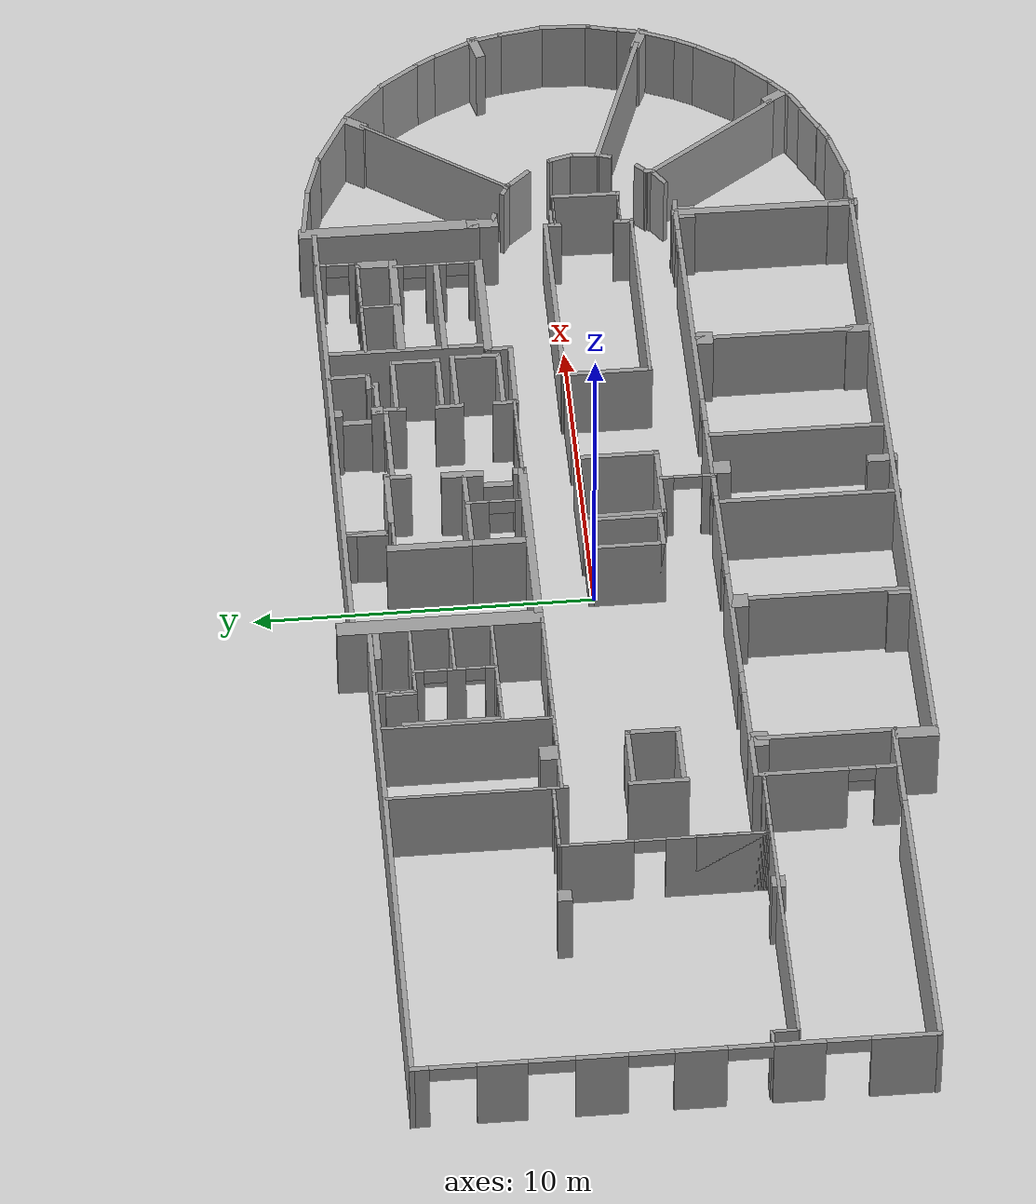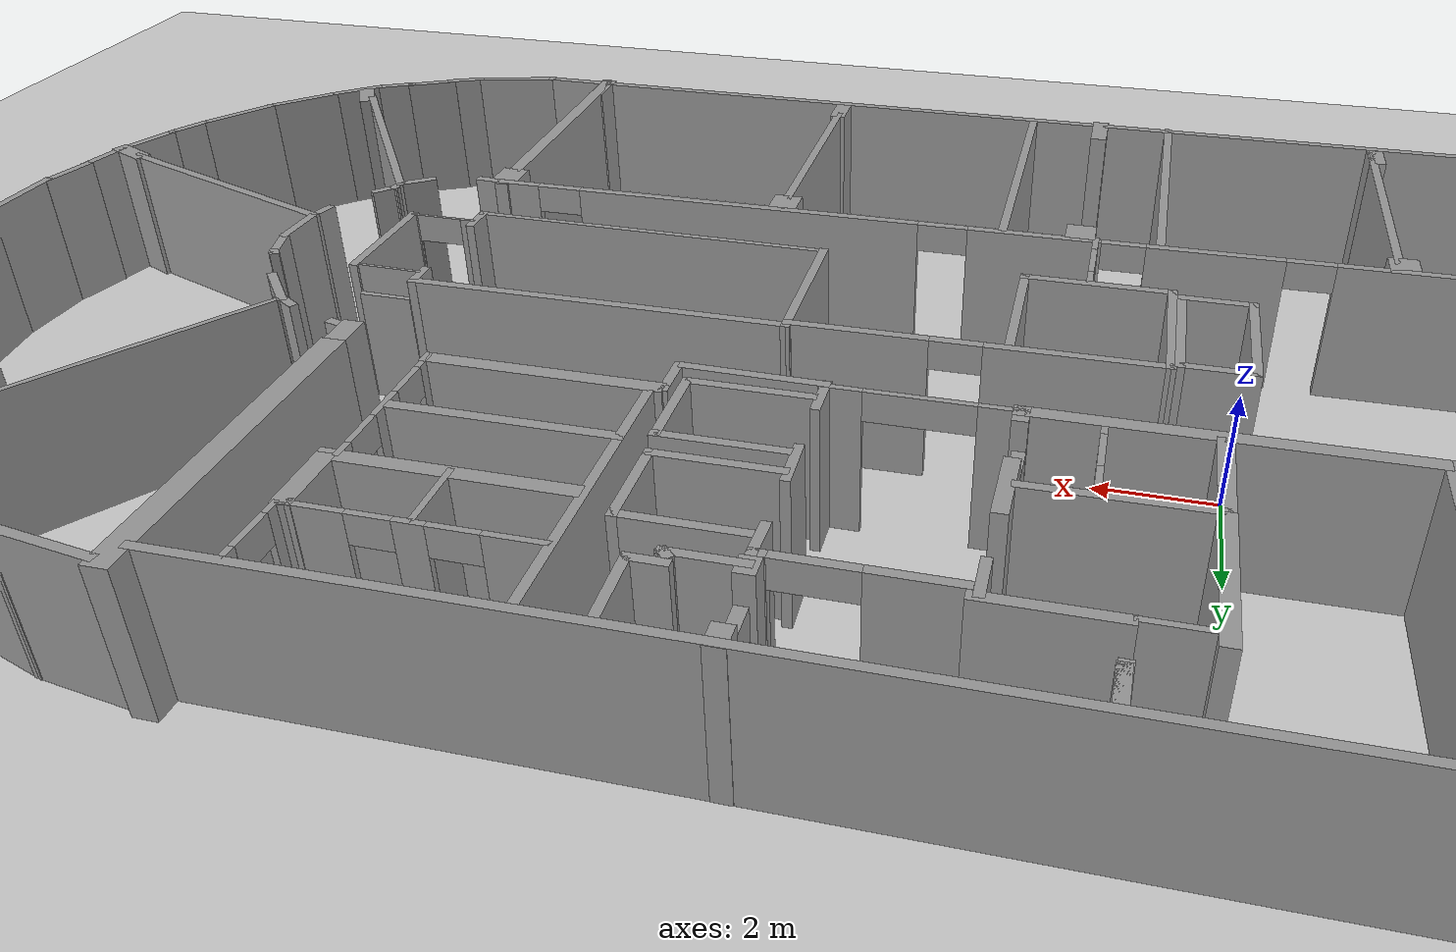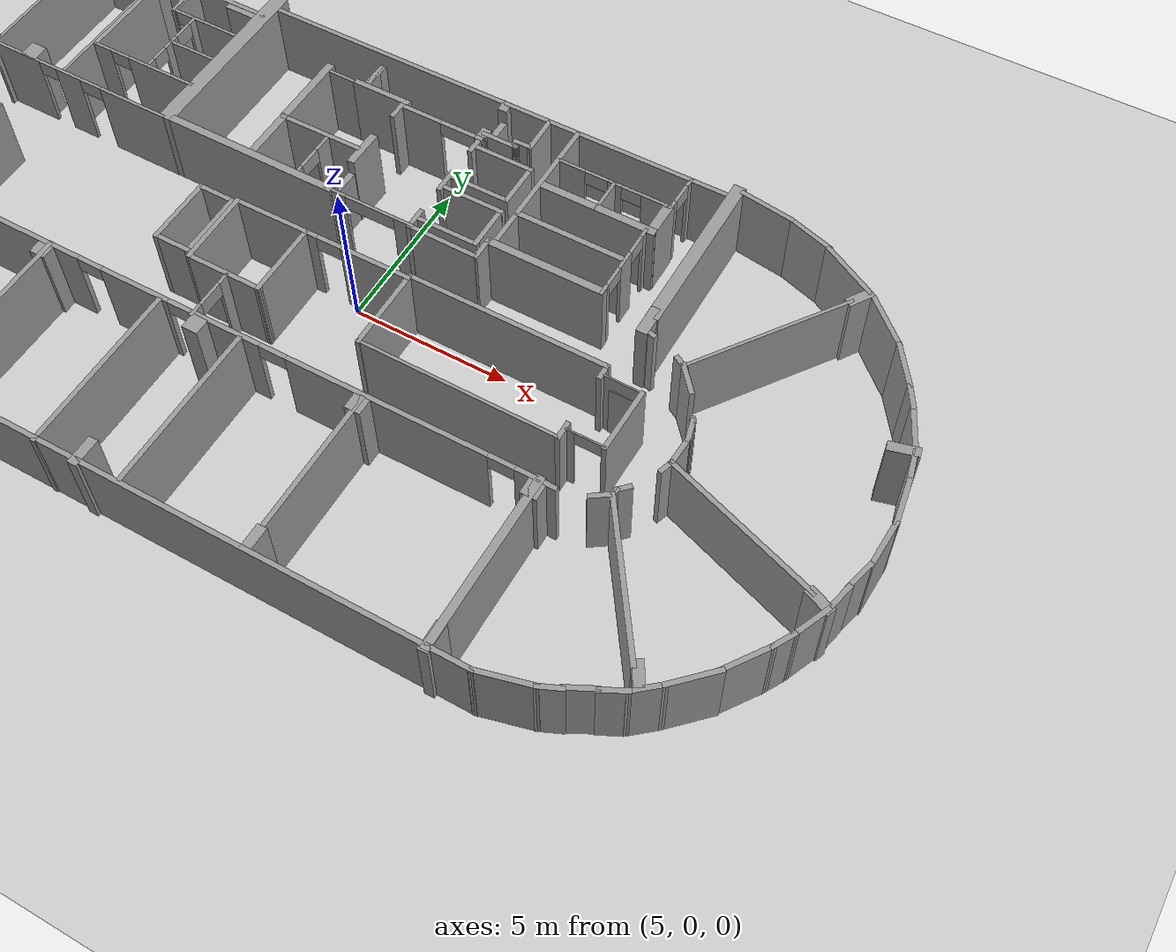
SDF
<sdf version="1.8">
 <world name="6OG">
  <light name="sun" type="directional">
   <pose>0 0 10 0 0 0</pose>
   <diffuse>0.8 0.8 0.8 1</diffuse>
   <specular>0.2 0.2 0.2 1</specular>
   <attenuation>
    <range>1000</range>
    <constant>0.9</constant>
    <linear>0.01</linear>
    <quadratic>0.001</quadratic>
   </attenuation>
   <direction>-0.5 0.1 -0.9</direction>
  </light>
  <model name="ground_plane">
   <static>true</static>
   <link name="link">
    <collision name="collision">
     <geometry><plane><normal>0 0 1</normal><size>1900 200</size></plane></geometry>
    </collision>
    <visual name="visual">
     <geometry><plane><normal>0 0 1</normal><size>1900 200</size></plane></geometry>
     <material>
      <ambient>0.8 0.8 0.8 1</ambient>
      <diffuse>0.8 0.8 0.8 1</diffuse>
      <specular>0.8 0.8 0.8 1</specular>
     </material>
    </visual>
   </link>
  </model>
  <include><uri>file:///workspace/src/simulation/tiplu_world/models/6OG</uri><name>6OG</name></include>
 </world>
</sdf>

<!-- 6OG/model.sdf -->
<sdf version='1.7'>
  <model name='6OG'>
    <pose>1.31238 -0.721325 0 0 -0 0</pose>
    <link name='Door_0'>
      <collision name='Door_0_Collision'>
        <geometry>
          <box>
            <size>1.19786 0.2 2</size>
          </box>
        </geometry>
        <pose>0 0 1 0 -0 0</pose>
      </collision>
      <visual name='Door_0_Visual'>
        <pose>0 0 1 0 -0 0</pose>
        <geometry>
          <box>
            <size>1.19786 0.2 2</size>
          </box>
        </geometry>
        <material>
          <script>
            <uri>file://media/materials/scripts/gazebo.material</uri>
            <name>Gazebo/Grey</name>
          </script>
        </material>
      </visual>
      <pose>0.087917 7.30206 0 0 0 -1.59049</pose>
    </link>
    <link name='Door_2'>
      <collision name='Door_2_Collision'>
        <geometry>
          <box>
            <size>0.899685 0.2 2</size>
          </box>
        </geometry>
        <pose>0 0 1 0 -0 0</pose>
      </collision>
      <visual name='Door_2_Visual'>
        <pose>0 0 1 0 -0 0</pose>
        <geometry>
          <box>
            <size>0.899685 0.2 2</size>
          </box>
        </geometry>
        <material>
          <script>
            <uri>file://media/materials/scripts/gazebo.material</uri>
            <name>Gazebo/Grey</name>
          </script>
        </material>
      </visual>
      <pose>1.72146 3.29562 0 0 -0 1.55549</pose>
    </link>
    <link name='Door_36'>
      <collision name='Door_36_Collision'>
        <geometry>
          <box>
            <size>0.9 0.17 2</size>
          </box>
        </geometry>
        <pose>0 0 1 0 -0 0</pose>
      </collision>
      <visual name='Door_36_Visual'>
        <pose>0 0 1 0 -0 0</pose>
        <geometry>
          <box>
            <size>0.9 0.17 2</size>
          </box>
        </geometry>
        <material>
          <script>
            <uri>file://media/materials/scripts/gazebo.material</uri>
            <name>Gazebo/Grey</name>
          </script>
        </material>
      </visual>
      <pose>12.4661 0.747437 0 0 -0 0</pose>
    </link>
    <link name='Door_4'>
      <collision name='Door_4_Collision'>
        <geometry>
          <box>
            <size>1.26749 0.2 2</size>
          </box>
        </geometry>
        <pose>0 0 1 0 -0 0</pose>
      </collision>
      <visual name='Door_4_Visual'>
        <pose>0 0 1 0 -0 0</pose>
        <geometry>
          <box>
            <size>1.26749 0.2 2</size>
          </box>
        </geometry>
        <material>
          <script>
            <uri>file://media/materials/scripts/gazebo.material</uri>
            <name>Gazebo/Grey</name>
          </script>
        </material>
      </visual>
      <pose>0.083059 7.28752 0 0 0 -1.60699</pose>
    </link>
    <link name='Door_6'>
      <collision name='Door_6_Collision'>
        <geometry>
          <box>
            <size>0.918451 0.2 2</size>
          </box>
        </geometry>
        <pose>0 0 1 0 -0 0</pose>
      </collision>
      <visual name='Door_6_Visual'>
        <pose>0 0 1 0 -0 0</pose>
        <geometry>
          <box>
            <size>0.918451 0.2 2</size>
          </box>
        </geometry>
        <material>
          <script>
            <uri>file://media/materials/scripts/gazebo.material</uri>
            <name>Gazebo/Grey</name>
          </script>
        </material>
      </visual>
      <pose>4.56986 7.23651 0 0 -0 -1.56937</pose>
    </link>
    <link name='Wall_100'>
      <collision name='Wall_100_Collision'>
        <geometry>
          <box>
            <size>0.95 0.35 2.5</size>
          </box>
        </geometry>
        <pose>0 0 1.25 0 -0 0</pose>
      </collision>
      <visual name='Wall_100_Visual'>
        <pose>0 0 1.25 0 -0 0</pose>
        <geometry>
          <box>
            <size>0.95 0.35 2.5</size>
          </box>
        </geometry>
        <material>
          <script>
            <uri>file://media/materials/scripts/gazebo.material</uri>
            <name>Gazebo/Grey</name>
          </script>
          <ambient>1 1 1 1</ambient>
        </material>
        <meta>
          <layer>0</layer>
        </meta>
      </visual>
      <pose>12.0183 2.92132 0 0 -0 -1.5708</pose>
    </link>
    <link name='Wall_102'>
      <collision name='Wall_102_Collision'>
        <geometry>
          <box>
            <size>0.5 0.15 2.5</size>
          </box>
        </geometry>
        <pose>0 0 1.25 0 -0 0</pose>
      </collision>
      <visual name='Wall_102_Visual'>
        <pose>0 0 1.25 0 -0 0</pose>
        <geometry>
          <box>
            <size>0.5 0.15 2.5</size>
          </box>
        </geometry>
        <material>
          <script>
            <uri>file://media/materials/scripts/gazebo.material</uri>
            <name>Gazebo/Grey</name>
          </script>
          <ambient>1 1 1 1</ambient>
        </material>
        <meta>
          <layer>0</layer>
        </meta>
      </visual>
      <pose>12.1874 2.57603 0 0 -0 -0.261799</pose>
    </link>
    <link name='Wall_104'>
      <collision name='Wall_104_Collision'>
        <geometry>
          <box>
            <size>0.5 0.15 2.5</size>
          </box>
        </geometry>
        <pose>0 0 1.25 0 -0 0</pose>
      </collision>
      <visual name='Wall_104_Visual'>
        <pose>0 0 1.25 0 -0 0</pose>
        <geometry>
          <box>
            <size>0.5 0.15 2.5</size>
          </box>
        </geometry>
        <material>
          <script>
            <uri>file://media/materials/scripts/gazebo.material</uri>
            <name>Gazebo/Grey</name>
          </script>
          <ambient>1 1 1 1</ambient>
        </material>
        <meta>
          <layer>0</layer>
        </meta>
      </visual>
      <pose>13.4058 2.1061 0 0 -0 -0.523599</pose>
    </link>
    <link name='Wall_105'>
      <collision name='Wall_105_Collision'>
        <geometry>
          <box>
            <size>0.22734 0.15 2.5</size>
          </box>
        </geometry>
        <pose>0 0 1.25 0 -0 0</pose>
      </collision>
      <visual name='Wall_105_Visual'>
        <pose>0 0 1.25 0 -0 0</pose>
        <geometry>
          <box>
            <size>0.22734 0.15 2.5</size>
          </box>
        </geometry>
        <material>
          <script>
            <uri>file://media/materials/scripts/gazebo.material</uri>
            <name>Gazebo/Grey</name>
          </script>
          <ambient>1 1 1 1</ambient>
        </material>
        <meta>
          <layer>0</layer>
        </meta>
      </visual>
      <pose>13.5318 2.03252 0 0 -0 2.29045</pose>
    </link>
    <link name='Wall_106'>
      <collision name='Wall_106_Collision'>
        <geometry>
          <box>
            <size>1.04476 0.15 2.5</size>
          </box>
        </geometry>
        <pose>0 0 1.25 0 -0 0</pose>
      </collision>
      <visual name='Wall_106_Visual'>
        <pose>0 0 1.25 0 -0 0</pose>
        <geometry>
          <box>
            <size>1.04476 0.15 2.5</size>
          </box>
        </geometry>
        <material>
          <script>
            <uri>file://media/materials/scripts/gazebo.material</uri>
            <name>Gazebo/Grey</name>
          </script>
          <ambient>1 1 1 1</ambient>
        </material>
        <meta>
          <layer>0</layer>
        </meta>
      </visual>
      <pose>13.7989 1.72314 0 0 -0 -0.858023</pose>
    </link>
    <link name='Wall_108'>
      <collision name='Wall_108_Collision'>
        <geometry>
          <box>
            <size>0.209111 0.15 2.5</size>
          </box>
        </geometry>
        <pose>0 0 1.25 0 -0 0</pose>
      </collision>
      <visual name='Wall_108_Visual'>
        <pose>0 0 1.25 0 -0 0</pose>
        <geometry>
          <box>
            <size>0.209111 0.15 2.5</size>
          </box>
        </geometry>
        <material>
          <script>
            <uri>file://media/materials/scripts/gazebo.material</uri>
            <name>Gazebo/Grey</name>
          </script>
          <ambient>1 1 1 1</ambient>
        </material>
        <meta>
          <layer>0</layer>
        </meta>
      </visual>
      <pose>14.5312 0.622959 0 0 -0 -1.0472</pose>
    </link>
    <link name='Wall_109'>
      <collision name='Wall_109_Collision'>
        <geometry>
          <box>
            <size>0.75 0.15 2.5</size>
          </box>
        </geometry>
        <pose>0 0 1.25 0 -0 0</pose>
      </collision>
      <visual name='Wall_109_Visual'>
        <pose>0 0 1.25 0 -0 0</pose>
        <geometry>
          <box>
            <size>0.75 0.15 2.5</size>
          </box>
        </geometry>
        <material>
          <script>
            <uri>file://media/materials/scripts/gazebo.material</uri>
            <name>Gazebo/Grey</name>
          </script>
          <ambient>1 1 1 1</ambient>
        </material>
        <meta>
          <layer>0</layer>
        </meta>
      </visual>
      <pose>14.6237 0.307586 0 0 -0 -1.309</pose>
    </link>
    <link name='Wall_110'>
      <collision name='Wall_110_Collision'>
        <geometry>
          <box>
            <size>0.984416 0.15 2.5</size>
          </box>
        </geometry>
        <pose>0 0 1.25 0 -0 0</pose>
      </collision>
      <visual name='Wall_110_Visual'>
        <pose>0 0 1.25 0 -0 0</pose>
        <geometry>
          <box>
            <size>0.984416 0.15 2.5</size>
          </box>
        </geometry>
        <material>
          <script>
            <uri>file://media/materials/scripts/gazebo.material</uri>
            <name>Gazebo/Grey</name>
          </script>
          <ambient>1 1 1 1</ambient>
        </material>
        <meta>
          <layer>0</layer>
        </meta>
      </visual>
      <pose>14.6797 -0.398842 0 0 -0 -1.62254</pose>
    </link>
    <link name='Wall_111'>
      <collision name='Wall_111_Collision'>
        <geometry>
          <box>
            <size>0.513961 0.15 2.5</size>
          </box>
        </geometry>
        <pose>0 0 1.25 0 -0 0</pose>
      </collision>
      <visual name='Wall_111_Visual'>
        <pose>0 0 1.25 0 -0 0</pose>
        <geometry>
          <box>
            <size>0.513961 0.15 2.5</size>
          </box>
        </geometry>
        <material>
          <script>
            <uri>file://media/materials/scripts/gazebo.material</uri>
            <name>Gazebo/Grey</name>
          </script>
          <ambient>1 1 1 1</ambient>
        </material>
        <meta>
          <layer>0</layer>
        </meta>
      </visual>
      <pose>14.6021 -0.988619 0 0 -0 -1.88399</pose>
    </link>
    <link name='Wall_114'>
      <collision name='Wall_114_Collision'>
        <geometry>
          <box>
            <size>0.5 0.15 2.5</size>
          </box>
        </geometry>
        <pose>0 0 1.25 0 -0 0</pose>
      </collision>
      <visual name='Wall_114_Visual'>
        <pose>0 0 1.25 0 -0 0</pose>
        <geometry>
          <box>
            <size>0.5 0.15 2.5</size>
          </box>
        </geometry>
        <material>
          <script>
            <uri>file://media/materials/scripts/gazebo.material</uri>
            <name>Gazebo/Grey</name>
          </script>
          <ambient>1 1 1 1</ambient>
        </material>
        <meta>
          <layer>0</layer>
        </meta>
      </visual>
      <pose>13.9473 -2.10821 0 0 -0 -2.35619</pose>
    </link>
    <link name='Wall_115'>
      <collision name='Wall_115_Collision'>
        <geometry>
          <box>
            <size>0.321868 0.15 2.5</size>
          </box>
        </geometry>
        <pose>0 0 1.25 0 -0 0</pose>
      </collision>
      <visual name='Wall_115_Visual'>
        <pose>0 0 1.25 0 -0 0</pose>
        <geometry>
          <box>
            <size>0.321868 0.15 2.5</size>
          </box>
        </geometry>
        <material>
          <script>
            <uri>file://media/materials/scripts/gazebo.material</uri>
            <name>Gazebo/Grey</name>
          </script>
          <ambient>1 1 1 1</ambient>
        </material>
        <meta>
          <layer>0</layer>
        </meta>
      </visual>
      <pose>13.8137 -2.31732 0 0 -0 -1.68575</pose>
    </link>
    <link name='Wall_116'>
      <collision name='Wall_116_Collision'>
        <geometry>
          <box>
            <size>0.725331 0.15 2.5</size>
          </box>
        </geometry>
        <pose>0 0 1.25 0 -0 0</pose>
      </collision>
      <visual name='Wall_116_Visual'>
        <pose>0 0 1.25 0 -0 0</pose>
        <geometry>
          <box>
            <size>0.725331 0.15 2.5</size>
          </box>
        </geometry>
        <material>
          <script>
            <uri>file://media/materials/scripts/gazebo.material</uri>
            <name>Gazebo/Grey</name>
          </script>
          <ambient>1 1 1 1</ambient>
        </material>
        <meta>
          <layer>0</layer>
        </meta>
      </visual>
      <pose>13.5662 -2.56481 0 0 -0 -2.54289</pose>
    </link>
    <link name='Wall_119'>
      <collision name='Wall_119_Collision'>
        <geometry>
          <box>
            <size>5.27558 0.1 2.5</size>
          </box>
        </geometry>
        <pose>0 0 1.25 0 -0 0</pose>
      </collision>
      <visual name='Wall_119_Visual'>
        <pose>0 0 1.25 0 -0 0</pose>
        <geometry>
          <box>
            <size>5.27558 0.1 2.5</size>
          </box>
        </geometry>
        <material>
          <script>
            <uri>file://media/materials/scripts/gazebo.material</uri>
            <name>Gazebo/Grey</name>
          </script>
          <ambient>1 1 1 1</ambient>
        </material>
        <meta>
          <layer>0</layer>
        </meta>
      </visual>
      <pose>15.0256 4.15139 0 0 -0 0.951992</pose>
    </link>
    <link name='Wall_12'>
      <collision name='Wall_12_Collision'>
        <geometry>
          <box>
            <size>0.45 0.1 2.5</size>
          </box>
        </geometry>
        <pose>0 0 1.25 0 -0 0</pose>
      </collision>
      <visual name='Wall_12_Visual'>
        <pose>0 0 1.25 0 -0 0</pose>
        <geometry>
          <box>
            <size>0.45 0.1 2.5</size>
          </box>
        </geometry>
        <material>
          <script>
            <uri>file://media/materials/scripts/gazebo.material</uri>
            <name>Gazebo/Grey</name>
          </script>
          <ambient>1 1 1 1</ambient>
        </material>
        <meta>
          <layer>0</layer>
        </meta>
      </visual>
      <pose>-20.0884 -2.49467 0 0 -0 0</pose>
    </link>
    <link name='Wall_121'>
      <collision name='Wall_121_Collision'>
        <geometry>
          <box>
            <size>5.16587 0.15 2.5</size>
          </box>
        </geometry>
        <pose>0 0 1.25 0 -0 0</pose>
      </collision>
      <visual name='Wall_121_Visual'>
        <pose>0 0 1.25 0 -0 0</pose>
        <geometry>
          <box>
            <size>5.16587 0.15 2.5</size>
          </box>
        </geometry>
        <material>
          <script>
            <uri>file://media/materials/scripts/gazebo.material</uri>
            <name>Gazebo/Grey</name>
          </script>
          <ambient>1 1 1 1</ambient>
        </material>
        <meta>
          <layer>0</layer>
        </meta>
      </visual>
      <pose>17.0296 -1.63158 0 0 -0 -0.331438</pose>
    </link>
    <link name='Wall_123'>
      <collision name='Wall_123_Collision'>
        <geometry>
          <box>
            <size>4.90369 0.15 2.5</size>
          </box>
        </geometry>
        <pose>0 0 1.25 0 -0 0</pose>
      </collision>
      <visual name='Wall_123_Visual'>
        <pose>0 0 1.25 0 -0 0</pose>
        <geometry>
          <box>
            <size>4.90369 0.15 2.5</size>
          </box>
        </geometry>
        <material>
          <script>
            <uri>file://media/materials/scripts/gazebo.material</uri>
            <name>Gazebo/Grey</name>
          </script>
          <ambient>1 1 1 1</ambient>
        </material>
        <meta>
          <layer>0</layer>
        </meta>
      </visual>
      <pose>15.158 -4.35602 0 0 -0 -0.964591</pose>
    </link>
    <link name='Wall_125'>
      <collision name='Wall_125_Collision'>
        <geometry>
          <box>
            <size>0.75 0.3 2.5</size>
          </box>
        </geometry>
        <pose>0 0 1.25 0 -0 0</pose>
      </collision>
      <visual name='Wall_125_Visual'>
        <pose>0 0 1.25 0 -0 0</pose>
        <geometry>
          <box>
            <size>0.75 0.3 2.5</size>
          </box>
        </geometry>
        <material>
          <script>
            <uri>file://media/materials/scripts/gazebo.material</uri>
            <name>Gazebo/Grey</name>
          </script>
          <ambient>1 1 1 1</ambient>
        </material>
        <meta>
          <layer>0</layer>
        </meta>
      </visual>
      <pose>6.65963 -7.90667 0 0 -0 1.5708</pose>
    </link>
    <link name='Wall_127'>
      <collision name='Wall_127_Collision'>
        <geometry>
          <box>
            <size>0.900344 0.3 2.5</size>
          </box>
        </geometry>
        <pose>0 0 1.25 0 -0 0</pose>
      </collision>
      <visual name='Wall_127_Visual'>
        <pose>0 0 1.25 0 -0 0</pose>
        <geometry>
          <box>
            <size>0.900344 0.3 2.5</size>
          </box>
        </geometry>
        <material>
          <script>
            <uri>file://media/materials/scripts/gazebo.material</uri>
            <name>Gazebo/Grey</name>
          </script>
          <ambient>1 1 1 1</ambient>
        </material>
        <meta>
          <layer>0</layer>
        </meta>
      </visual>
      <pose>1.34662 -8.00667 0 0 -0 -1.5708</pose>
    </link>
    <link name='Wall_129'>
      <collision name='Wall_129_Collision'>
        <geometry>
          <box>
            <size>0.65 0.3 2.5</size>
          </box>
        </geometry>
        <pose>0 0 1.25 0 -0 0</pose>
      </collision>
      <visual name='Wall_129_Visual'>
        <pose>0 0 1.25 0 -0 0</pose>
        <geometry>
          <box>
            <size>0.65 0.3 2.5</size>
          </box>
        </geometry>
        <material>
          <script>
            <uri>file://media/materials/scripts/gazebo.material</uri>
            <name>Gazebo/Grey</name>
          </script>
          <ambient>1 1 1 1</ambient>
        </material>
        <meta>
          <layer>0</layer>
        </meta>
      </visual>
      <pose>-3.93079 -7.87854 0 0 -0 -1.5708</pose>
    </link>
    <link name='Wall_13'>
      <collision name='Wall_13_Collision'>
        <geometry>
          <box>
            <size>0.83757 0.1 2.5</size>
          </box>
        </geometry>
        <pose>0 0 1.25 0 -0 0</pose>
      </collision>
      <visual name='Wall_13_Visual'>
        <pose>0 0 1.25 0 -0 0</pose>
        <geometry>
          <box>
            <size>0.83757 0.1 2.5</size>
          </box>
        </geometry>
        <material>
          <script>
            <uri>file://media/materials/scripts/gazebo.material</uri>
            <name>Gazebo/Grey</name>
          </script>
          <ambient>1 1 1 1</ambient>
        </material>
        <meta>
          <layer>0</layer>
        </meta>
      </visual>
      <pose>-19.9064 -2.86318 0 0 -0 -1.5518</pose>
    </link>
    <link name='Wall_131'>
      <collision name='Wall_131_Collision'>
        <geometry>
          <box>
            <size>0.81032 0.3 2.5</size>
          </box>
        </geometry>
        <pose>0 0 1.25 0 -0 0</pose>
      </collision>
      <visual name='Wall_131_Visual'>
        <pose>0 0 1.25 0 -0 0</pose>
        <geometry>
          <box>
            <size>0.81032 0.3 2.5</size>
          </box>
        </geometry>
        <material>
          <script>
            <uri>file://media/materials/scripts/gazebo.material</uri>
            <name>Gazebo/Grey</name>
          </script>
          <ambient>1 1 1 1</ambient>
        </material>
        <meta>
          <layer>0</layer>
        </meta>
      </visual>
      <pose>16.6656 6.47332 0 0 -0 -2.14684</pose>
    </link>
    <link name='Wall_133'>
      <collision name='Wall_133_Collision'>
        <geometry>
          <box>
            <size>0.900367 0.3 2.5</size>
          </box>
        </geometry>
        <pose>0 0 1.25 0 -0 0</pose>
      </collision>
      <visual name='Wall_133_Visual'>
        <pose>0 0 1.25 0 -0 0</pose>
        <geometry>
          <box>
            <size>0.900367 0.3 2.5</size>
          </box>
        </geometry>
        <material>
          <script>
            <uri>file://media/materials/scripts/gazebo.material</uri>
            <name>Gazebo/Grey</name>
          </script>
          <ambient>1 1 1 1</ambient>
        </material>
        <meta>
          <layer>0</layer>
        </meta>
      </visual>
      <pose>19.6646 2.49982 0 0 -0 -2.88045</pose>
    </link>
    <link name='Wall_135'>
      <collision name='Wall_135_Collision'>
        <geometry>
          <box>
            <size>0.847308 0.3 2.5</size>
          </box>
        </geometry>
        <pose>0 0 1.25 0 -0 0</pose>
      </collision>
      <visual name='Wall_135_Visual'>
        <pose>0 0 1.25 0 -0 0</pose>
        <geometry>
          <box>
            <size>0.847308 0.3 2.5</size>
          </box>
        </geometry>
        <material>
          <script>
            <uri>file://media/materials/scripts/gazebo.material</uri>
            <name>Gazebo/Grey</name>
          </script>
          <ambient>1 1 1 1</ambient>
        </material>
        <meta>
          <layer>0</layer>
        </meta>
      </visual>
      <pose>19.6259 -2.55317 0 0 -0 2.74582</pose>
    </link>
    <link name='Wall_137'>
      <collision name='Wall_137_Collision'>
        <geometry>
          <box>
            <size>0.75 0.3 2.5</size>
          </box>
        </geometry>
        <pose>0 0 1.25 0 -0 0</pose>
      </collision>
      <visual name='Wall_137_Visual'>
        <pose>0 0 1.25 0 -0 0</pose>
        <geometry>
          <box>
            <size>0.75 0.3 2.5</size>
          </box>
        </geometry>
        <material>
          <script>
            <uri>file://media/materials/scripts/gazebo.material</uri>
            <name>Gazebo/Grey</name>
          </script>
          <ambient>1 1 1 1</ambient>
        </material>
        <meta>
          <layer>0</layer>
        </meta>
      </visual>
      <pose>16.7111 -6.42082 0 0 -0 -1.0472</pose>
    </link>
    <link name='Wall_139'>
      <collision name='Wall_139_Collision'>
        <geometry>
          <box>
            <size>0.899931 0.3 2.5</size>
          </box>
        </geometry>
        <pose>0 0 1.25 0 -0 0</pose>
      </collision>
      <visual name='Wall_139_Visual'>
        <pose>0 0 1.25 0 -0 0</pose>
        <geometry>
          <box>
            <size>0.899931 0.3 2.5</size>
          </box>
        </geometry>
        <material>
          <script>
            <uri>file://media/materials/scripts/gazebo.material</uri>
            <name>Gazebo/Grey</name>
          </script>
          <ambient>1 1 1 1</ambient>
        </material>
        <meta>
          <layer>0</layer>
        </meta>
      </visual>
      <pose>11.9746 -8.02468 0 0 -0 -1.5708</pose>
    </link>
    <link name='Wall_14'>
      <pose>-15.2569 -3.23786 0 0 -0 -0.001332</pose>
      <visual name='Wall_14_Visual_0'>
        <pose>-0.95658 0 1.25 0 -0 0</pose>
        <geometry>
          <box>
            <size>7.47141 0.1 2.5</size>
          </box>
        </geometry>
        <material>
          <script>
            <uri>file://media/materials/scripts/gazebo.material</uri>
            <name>Gazebo/Grey</name>
          </script>
          <ambient>1 1 1 1</ambient>
        </material>
        <meta>
          <layer>0</layer>
        </meta>
      </visual>
      <collision name='Wall_14_Collision_0'>
        <geometry>
          <box>
            <size>7.47141 0.1 2.5</size>
          </box>
        </geometry>
        <pose>-0.95658 0 1.25 0 -0 0</pose>
      </collision>
      <visual name='Wall_14_Visual_1'>
        <pose>4.14406 0 1.25 0 -0 0</pose>
        <geometry>
          <box>
            <size>1.09645 0.1 2.5</size>
          </box>
        </geometry>
        <material>
          <script>
            <uri>file://media/materials/scripts/gazebo.material</uri>
            <name>Gazebo/Grey</name>
          </script>
          <ambient>1 1 1 1</ambient>
        </material>
        <meta>
          <layer>0</layer>
        </meta>
      </visual>
      <collision name='Wall_14_Collision_1'>
        <geometry>
          <box>
            <size>1.09645 0.1 2.5</size>
          </box>
        </geometry>
        <pose>4.14406 0 1.25 0 -0 0</pose>
      </collision>
      <visual name='Wall_14_Visual_2'>
        <pose>4.57201 0 1.25 0 -0 0</pose>
        <geometry>
          <box>
            <size>0.240551 0.1 2.5</size>
          </box>
        </geometry>
        <material>
          <script>
            <uri>file://media/materials/scripts/gazebo.material</uri>
            <name>Gazebo/Grey</name>
          </script>
          <ambient>1 1 1 1</ambient>
        </material>
        <meta>
          <layer>0</layer>
        </meta>
      </visual>
      <collision name='Wall_14_Collision_2'>
        <geometry>
          <box>
            <size>0.240551 0.1 2.5</size>
          </box>
        </geometry>
        <pose>4.57201 0 1.25 0 -0 0</pose>
      </collision>
      <visual name='Wall_14_Visual_3'>
        <pose>3.17896 0 2.25 0 -0 0</pose>
        <geometry>
          <box>
            <size>0.799665 0.1 0.5</size>
          </box>
        </geometry>
        <material>
          <script>
            <uri>file://media/materials/scripts/gazebo.material</uri>
            <name>Gazebo/Grey</name>
          </script>
          <ambient>1 1 1 1</ambient>
        </material>
        <meta>
          <layer>0</layer>
        </meta>
      </visual>
      <collision name='Wall_14_Collision_3'>
        <geometry>
          <box>
            <size>0.799665 0.1 0.5</size>
          </box>
        </geometry>
        <pose>3.17896 0 2.25 0 -0 0</pose>
      </collision>
    </link>
    <link name='Wall_141'>
      <collision name='Wall_141_Collision'>
        <geometry>
          <box>
            <size>1.25 0.15 2.5</size>
          </box>
        </geometry>
        <pose>0 0 1.25 0 -0 0</pose>
      </collision>
      <visual name='Wall_141_Visual'>
        <pose>0 0 1.25 0 -0 0</pose>
        <geometry>
          <box>
            <size>1.25 0.15 2.5</size>
          </box>
        </geometry>
        <material>
          <script>
            <uri>file://media/materials/scripts/gazebo.material</uri>
            <name>Gazebo/Grey</name>
          </script>
          <ambient>1 1 1 1</ambient>
        </material>
        <meta>
          <layer>0</layer>
        </meta>
      </visual>
      <pose>-0.920949 -1.27644 0 0 -0 0</pose>
    </link>
    <link name='Wall_143'>
      <collision name='Wall_143_Collision'>
        <geometry>
          <box>
            <size>2.25 0.15 2.5</size>
          </box>
        </geometry>
        <pose>0 0 1.25 0 -0 0</pose>
      </collision>
      <visual name='Wall_143_Visual'>
        <pose>0 0 1.25 0 -0 0</pose>
        <geometry>
          <box>
            <size>2.25 0.15 2.5</size>
          </box>
        </geometry>
        <material>
          <script>
            <uri>file://media/materials/scripts/gazebo.material</uri>
            <name>Gazebo/Grey</name>
          </script>
          <ambient>1 1 1 1</ambient>
        </material>
        <meta>
          <layer>0</layer>
        </meta>
      </visual>
      <pose>-0.370949 -0.226441 0 0 -0 1.5708</pose>
    </link>
    <link name='Wall_144'>
      <collision name='Wall_144_Collision'>
        <geometry>
          <box>
            <size>1.25 0.15 2.5</size>
          </box>
        </geometry>
        <pose>0 0 1.25 0 -0 0</pose>
      </collision>
      <visual name='Wall_144_Visual'>
        <pose>0 0 1.25 0 -0 0</pose>
        <geometry>
          <box>
            <size>1.25 0.15 2.5</size>
          </box>
        </geometry>
        <material>
          <script>
            <uri>file://media/materials/scripts/gazebo.material</uri>
            <name>Gazebo/Grey</name>
          </script>
          <ambient>1 1 1 1</ambient>
        </material>
        <meta>
          <layer>0</layer>
        </meta>
      </visual>
      <pose>-0.920949 0.823559 0 0 -0 3.14159</pose>
    </link>
    <link name='Wall_145'>
      <collision name='Wall_145_Collision'>
        <geometry>
          <box>
            <size>2.25 0.15 2.5</size>
          </box>
        </geometry>
        <pose>0 0 1.25 0 -0 0</pose>
      </collision>
      <visual name='Wall_145_Visual'>
        <pose>0 0 1.25 0 -0 0</pose>
        <geometry>
          <box>
            <size>2.25 0.15 2.5</size>
          </box>
        </geometry>
        <material>
          <script>
            <uri>file://media/materials/scripts/gazebo.material</uri>
            <name>Gazebo/Grey</name>
          </script>
          <ambient>1 1 1 1</ambient>
        </material>
        <meta>
          <layer>0</layer>
        </meta>
      </visual>
      <pose>-1.47095 -0.226441 0 0 -0 -1.5708</pose>
    </link>
    <link name='Wall_147'>
      <pose>2.6386 0.919145 0 0 -0 -3.13618</pose>
      <visual name='Wall_147_Visual_0'>
        <pose>-1.82194 0 1.25 0 -0 0</pose>
        <geometry>
          <box>
            <size>2.28461 0.15 2.5</size>
          </box>
        </geometry>
        <material>
          <script>
            <uri>file://media/materials/scripts/gazebo.material</uri>
            <name>Gazebo/Grey</name>
          </script>
          <ambient>1 1 1 1</ambient>
        </material>
        <meta>
          <layer>0</layer>
        </meta>
      </visual>
      <collision name='Wall_147_Collision_0'>
        <geometry>
          <box>
            <size>2.28461 0.15 2.5</size>
          </box>
        </geometry>
        <pose>-1.82194 0 1.25 0 -0 0</pose>
      </collision>
      <visual name='Wall_147_Visual_1'>
        <pose>1.55172 0 1.25 0 -0 0</pose>
        <geometry>
          <box>
            <size>2.82505 0.15 2.5</size>
          </box>
        </geometry>
        <material>
          <script>
            <uri>file://media/materials/scripts/gazebo.material</uri>
            <name>Gazebo/Grey</name>
          </script>
          <ambient>1 1 1 1</ambient>
        </material>
        <meta>
          <layer>0</layer>
        </meta>
      </visual>
      <collision name='Wall_147_Collision_1'>
        <geometry>
          <box>
            <size>2.82505 0.15 2.5</size>
          </box>
        </geometry>
        <pose>1.55172 0 1.25 0 -0 0</pose>
      </collision>
      <visual name='Wall_147_Visual_2'>
        <pose>-0.270218 0 2.25 0 -0 0</pose>
        <geometry>
          <box>
            <size>0.818833 0.15 0.5</size>
          </box>
        </geometry>
        <material>
          <script>
            <uri>file://media/materials/scripts/gazebo.material</uri>
            <name>Gazebo/Grey</name>
          </script>
          <ambient>1 1 1 1</ambient>
        </material>
        <meta>
          <layer>0</layer>
        </meta>
      </visual>
      <collision name='Wall_147_Collision_2'>
        <geometry>
          <box>
            <size>0.818833 0.15 0.5</size>
          </box>
        </geometry>
        <pose>-0.270218 0 2.25 0 -0 0</pose>
      </collision>
    </link>
    <link name='Wall_148'>
      <collision name='Wall_148_Collision'>
        <geometry>
          <box>
            <size>2.46575 0.15 2.5</size>
          </box>
        </geometry>
        <pose>0 0 1.25 0 -0 0</pose>
      </collision>
      <visual name='Wall_148_Visual'>
        <pose>0 0 1.25 0 -0 0</pose>
        <geometry>
          <box>
            <size>2.46575 0.15 2.5</size>
          </box>
        </geometry>
        <material>
          <script>
            <uri>file://media/materials/scripts/gazebo.material</uri>
            <name>Gazebo/Grey</name>
          </script>
          <ambient>1 1 1 1</ambient>
        </material>
        <meta>
          <layer>0</layer>
        </meta>
      </visual>
      <pose>-0.234954 -0.254268 0 0 -0 -1.55728</pose>
    </link>
    <link name='Wall_149'>
      <collision name='Wall_149_Collision'>
        <geometry>
          <box>
            <size>2.5 0.15 2.5</size>
          </box>
        </geometry>
        <pose>0 0 1.25 0 -0 0</pose>
      </collision>
      <visual name='Wall_149_Visual'>
        <pose>0 0 1.25 0 -0 0</pose>
        <geometry>
          <box>
            <size>2.5 0.15 2.5</size>
          </box>
        </geometry>
        <material>
          <script>
            <uri>file://media/materials/scripts/gazebo.material</uri>
            <name>Gazebo/Grey</name>
          </script>
          <ambient>1 1 1 1</ambient>
        </material>
        <meta>
          <layer>0</layer>
        </meta>
      </visual>
      <pose>0.955692 -1.41203 0 0 -0 0</pose>
    </link>
    <link name='Wall_150'>
      <collision name='Wall_150_Collision'>
        <geometry>
          <box>
            <size>2.47609 0.15 2.5</size>
          </box>
        </geometry>
        <pose>0 0 1.25 0 -0 0</pose>
      </collision>
      <visual name='Wall_150_Visual'>
        <pose>0 0 1.25 0 -0 0</pose>
        <geometry>
          <box>
            <size>2.47609 0.15 2.5</size>
          </box>
        </geometry>
        <material>
          <script>
            <uri>file://media/materials/scripts/gazebo.material</uri>
            <name>Gazebo/Grey</name>
          </script>
          <ambient>1 1 1 1</ambient>
        </material>
        <meta>
          <layer>0</layer>
        </meta>
      </visual>
      <pose>2.12389 -0.249053 0 0 -0 1.57665</pose>
    </link>
    <link name='Wall_152'>
      <pose>1.09478 -2.25411 0 0 -0 -1.5708</pose>
      <visual name='Wall_152_Visual_0'>
        <pose>-0.639021 0 1.25 0 -0 0</pose>
        <geometry>
          <box>
            <size>0.421958 0.1 2.5</size>
          </box>
        </geometry>
        <material>
          <script>
            <uri>file://media/materials/scripts/gazebo.material</uri>
            <name>Gazebo/Grey</name>
          </script>
          <ambient>1 1 1 1</ambient>
        </material>
        <meta>
          <layer>0</layer>
        </meta>
      </visual>
      <collision name='Wall_152_Collision_0'>
        <geometry>
          <box>
            <size>0.421958 0.1 2.5</size>
          </box>
        </geometry>
        <pose>-0.639021 0 1.25 0 -0 0</pose>
      </collision>
      <visual name='Wall_152_Visual_1'>
        <pose>0.627159 0 1.25 0 -0 0</pose>
        <geometry>
          <box>
            <size>0.445682 0.1 2.5</size>
          </box>
        </geometry>
        <material>
          <script>
            <uri>file://media/materials/scripts/gazebo.material</uri>
            <name>Gazebo/Grey</name>
          </script>
          <ambient>1 1 1 1</ambient>
        </material>
        <meta>
          <layer>0</layer>
        </meta>
      </visual>
      <collision name='Wall_152_Collision_1'>
        <geometry>
          <box>
            <size>0.445682 0.1 2.5</size>
          </box>
        </geometry>
        <pose>0.627159 0 1.25 0 -0 0</pose>
      </collision>
      <visual name='Wall_152_Visual_2'>
        <pose>-0.011862 0 2.25 0 -0 0</pose>
        <geometry>
          <box>
            <size>0.83236 0.1 0.5</size>
          </box>
        </geometry>
        <material>
          <script>
            <uri>file://media/materials/scripts/gazebo.material</uri>
            <name>Gazebo/Grey</name>
          </script>
          <ambient>1 1 1 1</ambient>
        </material>
        <meta>
          <layer>0</layer>
        </meta>
      </visual>
      <collision name='Wall_152_Collision_2'>
        <geometry>
          <box>
            <size>0.83236 0.1 0.5</size>
          </box>
        </geometry>
        <pose>-0.011862 0 2.25 0 -0 0</pose>
      </collision>
    </link>
    <link name='Wall_154'>
      <collision name='Wall_154_Collision'>
        <geometry>
          <box>
            <size>0.54649 0.15 2.5</size>
          </box>
        </geometry>
        <pose>0 0 1.25 0 -0 0</pose>
      </collision>
      <visual name='Wall_154_Visual'>
        <pose>0 0 1.25 0 -0 0</pose>
        <geometry>
          <box>
            <size>0.54649 0.15 2.5</size>
          </box>
        </geometry>
        <material>
          <script>
            <uri>file://media/materials/scripts/gazebo.material</uri>
            <name>Gazebo/Grey</name>
          </script>
          <ambient>1 1 1 1</ambient>
        </material>
        <meta>
          <layer>0</layer>
        </meta>
      </visual>
      <pose>11.7651 0.820056 0 0 -0 1.5708</pose>
    </link>
    <link name='Wall_155'>
      <collision name='Wall_155_Collision'>
        <geometry>
          <box>
            <size>6.38735 0.15 2.5</size>
          </box>
        </geometry>
        <pose>0 0 1.25 0 -0 0</pose>
      </collision>
      <visual name='Wall_155_Visual'>
        <pose>0 0 1.25 0 -0 0</pose>
        <geometry>
          <box>
            <size>6.38735 0.15 2.5</size>
          </box>
        </geometry>
        <material>
          <script>
            <uri>file://media/materials/scripts/gazebo.material</uri>
            <name>Gazebo/Grey</name>
          </script>
          <ambient>1 1 1 1</ambient>
        </material>
        <meta>
          <layer>0</layer>
        </meta>
      </visual>
      <pose>8.64648 1.01823 0 0 -0 3.14159</pose>
    </link>
    <link name='Wall_156'>
      <collision name='Wall_156_Collision'>
        <geometry>
          <box>
            <size>2.71605 0.15 2.5</size>
          </box>
        </geometry>
        <pose>0 0 1.25 0 -0 0</pose>
      </collision>
      <visual name='Wall_156_Visual'>
        <pose>0 0 1.25 0 -0 0</pose>
        <geometry>
          <box>
            <size>2.71605 0.15 2.5</size>
          </box>
        </geometry>
        <material>
          <script>
            <uri>file://media/materials/scripts/gazebo.material</uri>
            <name>Gazebo/Grey</name>
          </script>
          <ambient>1 1 1 1</ambient>
        </material>
        <meta>
          <layer>0</layer>
        </meta>
      </visual>
      <pose>5.53322 -0.264721 0 0 -0 -1.56658</pose>
    </link>
    <link name='Wall_157'>
      <collision name='Wall_157_Collision'>
        <geometry>
          <box>
            <size>6.31617 0.1 2.5</size>
          </box>
        </geometry>
        <pose>0 0 1.25 0 -0 0</pose>
      </collision>
      <visual name='Wall_157_Visual'>
        <pose>0 0 1.25 0 -0 0</pose>
        <geometry>
          <box>
            <size>6.31617 0.1 2.5</size>
          </box>
        </geometry>
        <material>
          <script>
            <uri>file://media/materials/scripts/gazebo.material</uri>
            <name>Gazebo/Grey</name>
          </script>
          <ambient>1 1 1 1</ambient>
        </material>
        <meta>
          <layer>0</layer>
        </meta>
      </visual>
      <pose>8.64663 -1.56317 0 0 -0 -0.004987</pose>
    </link>
    <link name='Wall_158'>
      <collision name='Wall_158_Collision'>
        <geometry>
          <box>
            <size>0.619365 0.15 2.5</size>
          </box>
        </geometry>
        <pose>0 0 1.25 0 -0 0</pose>
      </collision>
      <visual name='Wall_158_Visual'>
        <pose>0 0 1.25 0 -0 0</pose>
        <geometry>
          <box>
            <size>0.619365 0.15 2.5</size>
          </box>
        </geometry>
        <material>
          <script>
            <uri>file://media/materials/scripts/gazebo.material</uri>
            <name>Gazebo/Grey</name>
          </script>
          <ambient>1 1 1 1</ambient>
        </material>
        <meta>
          <layer>0</layer>
        </meta>
      </visual>
      <pose>11.7547 -1.34411 0 0 -0 1.5706</pose>
    </link>
    <link name='Wall_16'>
      <pose>1.37952 -2.97983 0 0 -0 0.003787</pose>
      <visual name='Wall_16_Visual_0'>
        <pose>-9.76219 0 1.25 0 -0 0</pose>
        <geometry>
          <box>
            <size>1.83095 0.15 2.5</size>
          </box>
        </geometry>
        <material>
          <script>
            <uri>file://media/materials/scripts/gazebo.material</uri>
            <name>Gazebo/Grey</name>
          </script>
          <ambient>1 1 1 1</ambient>
        </material>
        <meta>
          <layer>0</layer>
        </meta>
      </visual>
      <collision name='Wall_16_Collision_0'>
        <geometry>
          <box>
            <size>1.83095 0.15 2.5</size>
          </box>
        </geometry>
        <pose>-9.76219 0 1.25 0 -0 0</pose>
      </collision>
      <visual name='Wall_16_Visual_1'>
        <pose>-6.14983 0 1.25 0 -0 0</pose>
        <geometry>
          <box>
            <size>3.83728 0.15 2.5</size>
          </box>
        </geometry>
        <material>
          <script>
            <uri>file://media/materials/scripts/gazebo.material</uri>
            <name>Gazebo/Grey</name>
          </script>
          <ambient>1 1 1 1</ambient>
        </material>
        <meta>
          <layer>0</layer>
        </meta>
      </visual>
      <collision name='Wall_16_Collision_1'>
        <geometry>
          <box>
            <size>3.83728 0.15 2.5</size>
          </box>
        </geometry>
        <pose>-6.14983 0 1.25 0 -0 0</pose>
      </collision>
      <visual name='Wall_16_Visual_2'>
        <pose>-2.27879 0 1.25 0 -0 0</pose>
        <geometry>
          <box>
            <size>2.29419 0.15 2.5</size>
          </box>
        </geometry>
        <material>
          <script>
            <uri>file://media/materials/scripts/gazebo.material</uri>
            <name>Gazebo/Grey</name>
          </script>
          <ambient>1 1 1 1</ambient>
        </material>
        <meta>
          <layer>0</layer>
        </meta>
      </visual>
      <collision name='Wall_16_Collision_2'>
        <geometry>
          <box>
            <size>2.29419 0.15 2.5</size>
          </box>
        </geometry>
        <pose>-2.27879 0 1.25 0 -0 0</pose>
      </collision>
      <visual name='Wall_16_Visual_3'>
        <pose>0.766685 0 1.25 0 -0 0</pose>
        <geometry>
          <box>
            <size>2.29436 0.15 2.5</size>
          </box>
        </geometry>
        <material>
          <script>
            <uri>file://media/materials/scripts/gazebo.material</uri>
            <name>Gazebo/Grey</name>
          </script>
          <ambient>1 1 1 1</ambient>
        </material>
        <meta>
          <layer>0</layer>
        </meta>
      </visual>
      <collision name='Wall_16_Collision_3'>
        <geometry>
          <box>
            <size>2.29436 0.15 2.5</size>
          </box>
        </geometry>
        <pose>0.766685 0 1.25 0 -0 0</pose>
      </collision>
      <visual name='Wall_16_Visual_4'>
        <pose>5.9325 0 1.25 0 -0 0</pose>
        <geometry>
          <box>
            <size>6.29139 0.15 2.5</size>
          </box>
        </geometry>
        <material>
          <script>
            <uri>file://media/materials/scripts/gazebo.material</uri>
            <name>Gazebo/Grey</name>
          </script>
          <ambient>1 1 1 1</ambient>
        </material>
        <meta>
          <layer>0</layer>
        </meta>
      </visual>
      <collision name='Wall_16_Collision_4'>
        <geometry>
          <box>
            <size>6.29139 0.15 2.5</size>
          </box>
        </geometry>
        <pose>5.9325 0 1.25 0 -0 0</pose>
      </collision>
      <visual name='Wall_16_Visual_5'>
        <pose>10.2806 0 1.25 0 -0 0</pose>
        <geometry>
          <box>
            <size>0.794157 0.15 2.5</size>
          </box>
        </geometry>
        <material>
          <script>
            <uri>file://media/materials/scripts/gazebo.material</uri>
            <name>Gazebo/Grey</name>
          </script>
          <ambient>1 1 1 1</ambient>
        </material>
        <meta>
          <layer>0</layer>
        </meta>
      </visual>
      <collision name='Wall_16_Collision_5'>
        <geometry>
          <box>
            <size>0.794157 0.15 2.5</size>
          </box>
        </geometry>
        <pose>10.2806 0 1.25 0 -0 0</pose>
      </collision>
      <visual name='Wall_16_Visual_6'>
        <pose>-8.45759 0 2.25 0 -0 0</pose>
        <geometry>
          <box>
            <size>0.778248 0.15 0.5</size>
          </box>
        </geometry>
        <material>
          <script>
            <uri>file://media/materials/scripts/gazebo.material</uri>
            <name>Gazebo/Grey</name>
          </script>
          <ambient>1 1 1 1</ambient>
        </material>
        <meta>
          <layer>0</layer>
        </meta>
      </visual>
      <collision name='Wall_16_Collision_6'>
        <geometry>
          <box>
            <size>0.778248 0.15 0.5</size>
          </box>
        </geometry>
        <pose>-8.45759 0 2.25 0 -0 0</pose>
      </collision>
      <visual name='Wall_16_Visual_7'>
        <pose>-3.82853 0 2.25 0 -0 0</pose>
        <geometry>
          <box>
            <size>0.805304 0.15 0.5</size>
          </box>
        </geometry>
        <material>
          <script>
            <uri>file://media/materials/scripts/gazebo.material</uri>
            <name>Gazebo/Grey</name>
          </script>
          <ambient>1 1 1 1</ambient>
        </material>
        <meta>
          <layer>0</layer>
        </meta>
      </visual>
      <collision name='Wall_16_Collision_7'>
        <geometry>
          <box>
            <size>0.805304 0.15 0.5</size>
          </box>
        </geometry>
        <pose>-3.82853 0 2.25 0 -0 0</pose>
      </collision>
      <visual name='Wall_16_Visual_8'>
        <pose>-0.756092 0 2.25 0 -0 0</pose>
        <geometry>
          <box>
            <size>0.751192 0.15 0.5</size>
          </box>
        </geometry>
        <material>
          <script>
            <uri>file://media/materials/scripts/gazebo.material</uri>
            <name>Gazebo/Grey</name>
          </script>
          <ambient>1 1 1 1</ambient>
        </material>
        <meta>
          <layer>0</layer>
        </meta>
      </visual>
      <collision name='Wall_16_Collision_8'>
        <geometry>
          <box>
            <size>0.751192 0.15 0.5</size>
          </box>
        </geometry>
        <pose>-0.756092 0 2.25 0 -0 0</pose>
      </collision>
      <visual name='Wall_16_Visual_9'>
        <pose>2.35034 0 2.25 0 -0 0</pose>
        <geometry>
          <box>
            <size>0.872944 0.15 0.5</size>
          </box>
        </geometry>
        <material>
          <script>
            <uri>file://media/materials/scripts/gazebo.material</uri>
            <name>Gazebo/Grey</name>
          </script>
          <ambient>1 1 1 1</ambient>
        </material>
        <meta>
          <layer>0</layer>
        </meta>
      </visual>
      <collision name='Wall_16_Collision_9'>
        <geometry>
          <box>
            <size>0.872944 0.15 0.5</size>
          </box>
        </geometry>
        <pose>2.35034 0 2.25 0 -0 0</pose>
      </collision>
      <visual name='Wall_16_Visual_10'>
        <pose>9.48085 0 2.25 0 -0 0</pose>
        <geometry>
          <box>
            <size>0.805304 0.15 0.5</size>
          </box>
        </geometry>
        <material>
          <script>
            <uri>file://media/materials/scripts/gazebo.material</uri>
            <name>Gazebo/Grey</name>
          </script>
          <ambient>1 1 1 1</ambient>
        </material>
        <meta>
          <layer>0</layer>
        </meta>
      </visual>
      <collision name='Wall_16_Collision_10'>
        <geometry>
          <box>
            <size>0.805304 0.15 0.5</size>
          </box>
        </geometry>
        <pose>9.48085 0 2.25 0 -0 0</pose>
      </collision>
    </link>
    <link name='Wall_161'>
      <pose>12.3699 -1.25563 0 0 -0 -3.14151</pose>
      <visual name='Wall_161_Visual_0'>
        <pose>-0.547313 0 1.25 0 -0 0</pose>
        <geometry>
          <box>
            <size>0.123954 0.05 2.5</size>
          </box>
        </geometry>
        <material>
          <script>
            <uri>file://media/materials/scripts/gazebo.material</uri>
            <name>Gazebo/Grey</name>
          </script>
          <ambient>1 1 1 1</ambient>
        </material>
        <meta>
          <layer>0</layer>
        </meta>
      </visual>
      <collision name='Wall_161_Collision_0'>
        <geometry>
          <box>
            <size>0.123954 0.05 2.5</size>
          </box>
        </geometry>
        <pose>-0.547313 0 1.25 0 -0 0</pose>
      </collision>
      <visual name='Wall_161_Visual_1'>
        <pose>0.471393 0 1.25 0 -0 0</pose>
        <geometry>
          <box>
            <size>0.275794 0.05 2.5</size>
          </box>
        </geometry>
        <material>
          <script>
            <uri>file://media/materials/scripts/gazebo.material</uri>
            <name>Gazebo/Grey</name>
          </script>
          <ambient>1 1 1 1</ambient>
        </material>
        <meta>
          <layer>0</layer>
        </meta>
      </visual>
      <collision name='Wall_161_Collision_1'>
        <geometry>
          <box>
            <size>0.275794 0.05 2.5</size>
          </box>
        </geometry>
        <pose>0.471393 0 1.25 0 -0 0</pose>
      </collision>
      <visual name='Wall_161_Visual_2'>
        <pose>-0.07592 0 2.25 0 -0 0</pose>
        <geometry>
          <box>
            <size>0.818832 0.05 0.5</size>
          </box>
        </geometry>
        <material>
          <script>
            <uri>file://media/materials/scripts/gazebo.material</uri>
            <name>Gazebo/Grey</name>
          </script>
          <ambient>1 1 1 1</ambient>
        </material>
        <meta>
          <layer>0</layer>
        </meta>
      </visual>
      <collision name='Wall_161_Collision_2'>
        <geometry>
          <box>
            <size>0.818832 0.05 0.5</size>
          </box>
        </geometry>
        <pose>-0.07592 0 2.25 0 -0 0</pose>
      </collision>
    </link>
    <link name='Wall_163'>
      <collision name='Wall_163_Collision'>
        <geometry>
          <box>
            <size>2.10446 0.15 2.5</size>
          </box>
        </geometry>
        <pose>0 0 1.25 0 -0 0</pose>
      </collision>
      <visual name='Wall_163_Visual'>
        <pose>0 0 1.25 0 -0 0</pose>
        <geometry>
          <box>
            <size>2.10446 0.15 2.5</size>
          </box>
        </geometry>
        <material>
          <script>
            <uri>file://media/materials/scripts/gazebo.material</uri>
            <name>Gazebo/Grey</name>
          </script>
          <ambient>1 1 1 1</ambient>
        </material>
        <meta>
          <layer>0</layer>
        </meta>
      </visual>
      <pose>12.9699 -0.278476 0 0 -0 1.55472</pose>
    </link>
    <link name='Wall_165'>
      <collision name='Wall_165_Collision'>
        <geometry>
          <box>
            <size>1.18719 0.05 2.5</size>
          </box>
        </geometry>
        <pose>0 0 1.25 0 -0 0</pose>
      </collision>
      <visual name='Wall_165_Visual'>
        <pose>0 0 1.25 0 -0 0</pose>
        <geometry>
          <box>
            <size>1.18719 0.05 2.5</size>
          </box>
        </geometry>
        <material>
          <script>
            <uri>file://media/materials/scripts/gazebo.material</uri>
            <name>Gazebo/Grey</name>
          </script>
          <ambient>1 1 1 1</ambient>
        </material>
        <meta>
          <layer>0</layer>
        </meta>
      </visual>
      <pose>12.3861 0.715825 0 0 -0 -0.018468</pose>
    </link>
    <link name='Wall_167'>
      <collision name='Wall_167_Collision'>
        <geometry>
          <box>
            <size>3.75 0.25 2.5</size>
          </box>
        </geometry>
        <pose>0 0 1.25 0 -0 0</pose>
      </collision>
      <visual name='Wall_167_Visual'>
        <pose>0 0 1.25 0 -0 0</pose>
        <geometry>
          <box>
            <size>3.75 0.25 2.5</size>
          </box>
        </geometry>
        <material>
          <script>
            <uri>file://media/materials/scripts/gazebo.material</uri>
            <name>Gazebo/Grey</name>
          </script>
          <ambient>1 1 1 1</ambient>
        </material>
        <meta>
          <layer>0</layer>
        </meta>
      </visual>
      <pose>8.62621 3.16732 0 0 -0 3.14159</pose>
    </link>
    <link name='Wall_170'>
      <pose>10.4326 4.40332 0 0 -0 1.5708</pose>
      <visual name='Wall_170_Visual_0'>
        <pose>-1.14539 0 1.25 0 -0 0</pose>
        <geometry>
          <box>
            <size>0.409541 0.1 2.5</size>
          </box>
        </geometry>
        <material>
          <script>
            <uri>file://media/materials/scripts/gazebo.material</uri>
            <name>Gazebo/Grey</name>
          </script>
          <ambient>1 1 1 1</ambient>
        </material>
        <meta>
          <layer>0</layer>
        </meta>
      </visual>
      <collision name='Wall_170_Collision_0'>
        <geometry>
          <box>
            <size>0.409541 0.1 2.5</size>
          </box>
        </geometry>
        <pose>-1.14539 0 1.25 0 -0 0</pose>
      </collision>
      <visual name='Wall_170_Visual_1'>
        <pose>0.044308 0 1.25 0 -0 0</pose>
        <geometry>
          <box>
            <size>0.622502 0.1 2.5</size>
          </box>
        </geometry>
        <material>
          <script>
            <uri>file://media/materials/scripts/gazebo.material</uri>
            <name>Gazebo/Grey</name>
          </script>
          <ambient>1 1 1 1</ambient>
        </material>
        <meta>
          <layer>0</layer>
        </meta>
      </visual>
      <collision name='Wall_170_Collision_1'>
        <geometry>
          <box>
            <size>0.622502 0.1 2.5</size>
          </box>
        </geometry>
        <pose>0.044308 0 1.25 0 -0 0</pose>
      </collision>
      <visual name='Wall_170_Visual_2'>
        <pose>1.1897 0 1.25 0 -0 0</pose>
        <geometry>
          <box>
            <size>0.320924 0.1 2.5</size>
          </box>
        </geometry>
        <material>
          <script>
            <uri>file://media/materials/scripts/gazebo.material</uri>
            <name>Gazebo/Grey</name>
          </script>
          <ambient>1 1 1 1</ambient>
        </material>
        <meta>
          <layer>0</layer>
        </meta>
      </visual>
      <collision name='Wall_170_Collision_2'>
        <geometry>
          <box>
            <size>0.320924 0.1 2.5</size>
          </box>
        </geometry>
        <pose>1.1897 0 1.25 0 -0 0</pose>
      </collision>
      <visual name='Wall_170_Visual_3'>
        <pose>-0.603784 0 2.25 0 -0 0</pose>
        <geometry>
          <box>
            <size>0.673682 0.1 0.5</size>
          </box>
        </geometry>
        <material>
          <script>
            <uri>file://media/materials/scripts/gazebo.material</uri>
            <name>Gazebo/Grey</name>
          </script>
          <ambient>1 1 1 1</ambient>
        </material>
        <meta>
          <layer>0</layer>
        </meta>
      </visual>
      <collision name='Wall_170_Collision_3'>
        <geometry>
          <box>
            <size>0.673682 0.1 0.5</size>
          </box>
        </geometry>
        <pose>-0.603784 0 2.25 0 -0 0</pose>
      </collision>
      <visual name='Wall_170_Visual_4'>
        <pose>0.6924 0 2.25 0 -0 0</pose>
        <geometry>
          <box>
            <size>0.673682 0.1 0.5</size>
          </box>
        </geometry>
        <material>
          <script>
            <uri>file://media/materials/scripts/gazebo.material</uri>
            <name>Gazebo/Grey</name>
          </script>
          <ambient>1 1 1 1</ambient>
        </material>
        <meta>
          <layer>0</layer>
        </meta>
      </visual>
      <collision name='Wall_170_Collision_4'>
        <geometry>
          <box>
            <size>0.673682 0.1 0.5</size>
          </box>
        </geometry>
        <pose>0.6924 0 2.25 0 -0 0</pose>
      </collision>
    </link>
    <link name='Wall_172'>
      <collision name='Wall_172_Collision'>
        <geometry>
          <box>
            <size>3.75 0.25 2.5</size>
          </box>
        </geometry>
        <pose>0 0 1.25 0 -0 0</pose>
      </collision>
      <visual name='Wall_172_Visual'>
        <pose>0 0 1.25 0 -0 0</pose>
        <geometry>
          <box>
            <size>3.75 0.25 2.5</size>
          </box>
        </geometry>
        <material>
          <script>
            <uri>file://media/materials/scripts/gazebo.material</uri>
            <name>Gazebo/Grey</name>
          </script>
          <ambient>1 1 1 1</ambient>
        </material>
        <meta>
          <layer>0</layer>
        </meta>
      </visual>
      <pose>8.84463 5.74233 0 0 -0 0</pose>
    </link>
    <link name='Wall_174'>
      <collision name='Wall_174_Collision'>
        <geometry>
          <box>
            <size>1.15 0.3 2.5</size>
          </box>
        </geometry>
        <pose>0 0 1.25 0 -0 0</pose>
      </collision>
      <visual name='Wall_174_Visual'>
        <pose>0 0 1.25 0 -0 0</pose>
        <geometry>
          <box>
            <size>1.15 0.3 2.5</size>
          </box>
        </geometry>
        <material>
          <script>
            <uri>file://media/materials/scripts/gazebo.material</uri>
            <name>Gazebo/Grey</name>
          </script>
          <ambient>1 1 1 1</ambient>
        </material>
        <meta>
          <layer>0</layer>
        </meta>
      </visual>
      <pose>10.5753 6.29403 0 0 -0 1.5708</pose>
    </link>
    <link name='Wall_176'>
      <collision name='Wall_176_Collision'>
        <geometry>
          <box>
            <size>1.16605 0.1 2.5</size>
          </box>
        </geometry>
        <pose>0 0 1.25 0 -0 0</pose>
      </collision>
      <visual name='Wall_176_Visual'>
        <pose>0 0 1.25 0 -0 0</pose>
        <geometry>
          <box>
            <size>1.16605 0.1 2.5</size>
          </box>
        </geometry>
        <material>
          <script>
            <uri>file://media/materials/scripts/gazebo.material</uri>
            <name>Gazebo/Grey</name>
          </script>
          <ambient>1 1 1 1</ambient>
        </material>
        <meta>
          <layer>0</layer>
        </meta>
      </visual>
      <pose>8.81064 6.24134 0 0 -0 -1.57082</pose>
    </link>
    <link name='Wall_178'>
      <pose>8.79013 6.80774 0 0 -0 0</pose>
      <visual name='Wall_178_Visual_0'>
        <pose>-1.3918 0 1.25 0 -0 0</pose>
        <geometry>
          <box>
            <size>0.912402 0.1 2.5</size>
          </box>
        </geometry>
        <material>
          <script>
            <uri>file://media/materials/scripts/gazebo.material</uri>
            <name>Gazebo/Grey</name>
          </script>
          <ambient>1 1 1 1</ambient>
        </material>
        <meta>
          <layer>0</layer>
        </meta>
      </visual>
      <collision name='Wall_178_Collision_0'>
        <geometry>
          <box>
            <size>0.912402 0.1 2.5</size>
          </box>
        </geometry>
        <pose>-1.3918 0 1.25 0 -0 0</pose>
      </collision>
      <visual name='Wall_178_Visual_1'>
        <pose>0.036476 0 1.25 0 -0 0</pose>
        <geometry>
          <box>
            <size>0.452763 0.1 2.5</size>
          </box>
        </geometry>
        <material>
          <script>
            <uri>file://media/materials/scripts/gazebo.material</uri>
            <name>Gazebo/Grey</name>
          </script>
          <ambient>1 1 1 1</ambient>
        </material>
        <meta>
          <layer>0</layer>
        </meta>
      </visual>
      <collision name='Wall_178_Collision_1'>
        <geometry>
          <box>
            <size>0.452763 0.1 2.5</size>
          </box>
        </geometry>
        <pose>0.036476 0 1.25 0 -0 0</pose>
      </collision>
      <visual name='Wall_178_Visual_2'>
        <pose>1.38198 0 1.25 0 -0 0</pose>
        <geometry>
          <box>
            <size>0.932034 0.1 2.5</size>
          </box>
        </geometry>
        <material>
          <script>
            <uri>file://media/materials/scripts/gazebo.material</uri>
            <name>Gazebo/Grey</name>
          </script>
          <ambient>1 1 1 1</ambient>
        </material>
        <meta>
          <layer>0</layer>
        </meta>
      </visual>
      <collision name='Wall_178_Collision_2'>
        <geometry>
          <box>
            <size>0.932034 0.1 2.5</size>
          </box>
        </geometry>
        <pose>1.38198 0 1.25 0 -0 0</pose>
      </collision>
      <visual name='Wall_178_Visual_3'>
        <pose>-0.562752 0 2.25 0 -0 0</pose>
        <geometry>
          <box>
            <size>0.745692 0.1 0.5</size>
          </box>
        </geometry>
        <material>
          <script>
            <uri>file://media/materials/scripts/gazebo.material</uri>
            <name>Gazebo/Grey</name>
          </script>
          <ambient>1 1 1 1</ambient>
        </material>
        <meta>
          <layer>0</layer>
        </meta>
      </visual>
      <collision name='Wall_178_Collision_3'>
        <geometry>
          <box>
            <size>0.745692 0.1 0.5</size>
          </box>
        </geometry>
        <pose>-0.562752 0 2.25 0 -0 0</pose>
      </collision>
      <visual name='Wall_178_Visual_4'>
        <pose>0.589412 0 2.25 0 -0 0</pose>
        <geometry>
          <box>
            <size>0.653108 0.1 0.5</size>
          </box>
        </geometry>
        <material>
          <script>
            <uri>file://media/materials/scripts/gazebo.material</uri>
            <name>Gazebo/Grey</name>
          </script>
          <ambient>1 1 1 1</ambient>
        </material>
        <meta>
          <layer>0</layer>
        </meta>
      </visual>
      <collision name='Wall_178_Collision_4'>
        <geometry>
          <box>
            <size>0.653108 0.1 0.5</size>
          </box>
        </geometry>
        <pose>0.589412 0 2.25 0 -0 0</pose>
      </collision>
    </link>
    <link name='Wall_179'>
      <collision name='Wall_179_Collision'>
        <geometry>
          <box>
            <size>0.227948 0.15 2.5</size>
          </box>
        </geometry>
        <pose>0 0 1.25 0 -0 0</pose>
      </collision>
      <visual name='Wall_179_Visual'>
        <pose>0 0 1.25 0 -0 0</pose>
        <geometry>
          <box>
            <size>0.227948 0.15 2.5</size>
          </box>
        </geometry>
        <material>
          <script>
            <uri>file://media/materials/scripts/gazebo.material</uri>
            <name>Gazebo/Grey</name>
          </script>
          <ambient>1 1 1 1</ambient>
        </material>
        <meta>
          <layer>0</layer>
        </meta>
      </visual>
      <pose>10.5564 6.80111 0 0 -0 -2.97062</pose>
    </link>
    <link name='Wall_18'>
      <collision name='Wall_18_Collision'>
        <geometry>
          <box>
            <size>5.25 0.15 2.5</size>
          </box>
        </geometry>
        <pose>0 0 1.25 0 -0 0</pose>
      </collision>
      <visual name='Wall_18_Visual'>
        <pose>0 0 1.25 0 -0 0</pose>
        <geometry>
          <box>
            <size>5.25 0.15 2.5</size>
          </box>
        </geometry>
        <material>
          <script>
            <uri>file://media/materials/scripts/gazebo.material</uri>
            <name>Gazebo/Grey</name>
          </script>
          <ambient>1 1 1 1</ambient>
        </material>
        <meta>
          <layer>0</layer>
        </meta>
      </visual>
      <pose>-3.85872 -5.5708 0 0 -0 -1.5708</pose>
    </link>
    <link name='Wall_182'>
      <pose>10.6623 7.42183 0 0 -0 -1.59346</pose>
      <visual name='Wall_182_Visual_0'>
        <pose>-0.47461 0 1.25 0 -0 0</pose>
        <geometry>
          <box>
            <size>0.298074 0.1 2.5</size>
          </box>
        </geometry>
        <material>
          <script>
            <uri>file://media/materials/scripts/gazebo.material</uri>
            <name>Gazebo/Grey</name>
          </script>
          <ambient>1 1 1 1</ambient>
        </material>
        <meta>
          <layer>0</layer>
        </meta>
      </visual>
      <collision name='Wall_182_Collision_0'>
        <geometry>
          <box>
            <size>0.298074 0.1 2.5</size>
          </box>
        </geometry>
        <pose>-0.47461 0 1.25 0 -0 0</pose>
      </collision>
      <visual name='Wall_182_Visual_1'>
        <pose>0.490233 0 1.25 0 -0 0</pose>
        <geometry>
          <box>
            <size>0.266828 0.1 2.5</size>
          </box>
        </geometry>
        <material>
          <script>
            <uri>file://media/materials/scripts/gazebo.material</uri>
            <name>Gazebo/Grey</name>
          </script>
          <ambient>1 1 1 1</ambient>
        </material>
        <meta>
          <layer>0</layer>
        </meta>
      </visual>
      <collision name='Wall_182_Collision_1'>
        <geometry>
          <box>
            <size>0.266828 0.1 2.5</size>
          </box>
        </geometry>
        <pose>0.490233 0 1.25 0 -0 0</pose>
      </collision>
      <visual name='Wall_182_Visual_2'>
        <pose>0.015623 0 2.25 0 -0 0</pose>
        <geometry>
          <box>
            <size>0.682393 0.1 0.5</size>
          </box>
        </geometry>
        <material>
          <script>
            <uri>file://media/materials/scripts/gazebo.material</uri>
            <name>Gazebo/Grey</name>
          </script>
          <ambient>1 1 1 1</ambient>
        </material>
        <meta>
          <layer>0</layer>
        </meta>
      </visual>
      <collision name='Wall_182_Collision_2'>
        <geometry>
          <box>
            <size>0.682393 0.1 0.5</size>
          </box>
        </geometry>
        <pose>0.015623 0 2.25 0 -0 0</pose>
      </collision>
    </link>
    <link name='Wall_184'>
      <collision name='Wall_184_Collision'>
        <geometry>
          <box>
            <size>4.75 0.15 2.5</size>
          </box>
        </geometry>
        <pose>0 0 1.25 0 -0 0</pose>
      </collision>
      <visual name='Wall_184_Visual'>
        <pose>0 0 1.25 0 -0 0</pose>
        <geometry>
          <box>
            <size>4.75 0.15 2.5</size>
          </box>
        </geometry>
        <material>
          <script>
            <uri>file://media/materials/scripts/gazebo.material</uri>
            <name>Gazebo/Grey</name>
          </script>
          <ambient>1 1 1 1</ambient>
        </material>
        <meta>
          <layer>0</layer>
        </meta>
      </visual>
      <pose>6.94397 5.64662 0 0 -0 -1.5708</pose>
    </link>
    <link name='Wall_186'>
      <collision name='Wall_186_Collision'>
        <geometry>
          <box>
            <size>3.52978 0.18 2.5</size>
          </box>
        </geometry>
        <pose>0 0 1.25 0 -0 0</pose>
      </collision>
      <visual name='Wall_186_Visual'>
        <pose>0 0 1.25 0 -0 0</pose>
        <geometry>
          <box>
            <size>3.52978 0.18 2.5</size>
          </box>
        </geometry>
        <material>
          <script>
            <uri>file://media/materials/scripts/gazebo.material</uri>
            <name>Gazebo/Grey</name>
          </script>
          <ambient>1 1 1 1</ambient>
        </material>
        <meta>
          <layer>0</layer>
        </meta>
      </visual>
      <pose>8.63462 4.45132 0 0 -0 0</pose>
    </link>
    <link name='Wall_190'>
      <collision name='Wall_190_Collision'>
        <geometry>
          <box>
            <size>2.84885 0.15 2.5</size>
          </box>
        </geometry>
        <pose>0 0 1.25 0 -0 0</pose>
      </collision>
      <visual name='Wall_190_Visual'>
        <pose>0 0 1.25 0 -0 0</pose>
        <geometry>
          <box>
            <size>2.84885 0.15 2.5</size>
          </box>
        </geometry>
        <material>
          <script>
            <uri>file://media/materials/scripts/gazebo.material</uri>
            <name>Gazebo/Grey</name>
          </script>
          <ambient>1 1 1 1</ambient>
        </material>
        <meta>
          <layer>0</layer>
        </meta>
      </visual>
      <pose>-7.82313 5.41713 0 0 -0 -1.5708</pose>
    </link>
    <link name='Wall_192'>
      <collision name='Wall_192_Collision'>
        <geometry>
          <box>
            <size>1.3 0.2 2.5</size>
          </box>
        </geometry>
        <pose>0 0 1.25 0 -0 0</pose>
      </collision>
      <visual name='Wall_192_Visual'>
        <pose>0 0 1.25 0 -0 0</pose>
        <geometry>
          <box>
            <size>1.3 0.2 2.5</size>
          </box>
        </geometry>
        <material>
          <script>
            <uri>file://media/materials/scripts/gazebo.material</uri>
            <name>Gazebo/Grey</name>
          </script>
          <ambient>1 1 1 1</ambient>
        </material>
        <meta>
          <layer>0</layer>
        </meta>
      </visual>
      <pose>-4.63537 7.32433 0 0 -0 0</pose>
    </link>
    <link name='Wall_194'>
      <collision name='Wall_194_Collision'>
        <geometry>
          <box>
            <size>5.75 0.25 2.5</size>
          </box>
        </geometry>
        <pose>0 0 1.25 0 -0 0</pose>
      </collision>
      <visual name='Wall_194_Visual'>
        <pose>0 0 1.25 0 -0 0</pose>
        <geometry>
          <box>
            <size>5.75 0.25 2.5</size>
          </box>
        </geometry>
        <material>
          <script>
            <uri>file://media/materials/scripts/gazebo.material</uri>
            <name>Gazebo/Grey</name>
          </script>
          <ambient>1 1 1 1</ambient>
        </material>
        <meta>
          <layer>0</layer>
        </meta>
      </visual>
      <pose>-1.01238 2.57845 0 0 -0 3.14159</pose>
    </link>
    <link name='Wall_196'>
      <collision name='Wall_196_Collision'>
        <geometry>
          <box>
            <size>1.79 0.24 2.5</size>
          </box>
        </geometry>
        <pose>0 0 1.25 0 -0 0</pose>
      </collision>
      <visual name='Wall_196_Visual'>
        <pose>0 0 1.25 0 -0 0</pose>
        <geometry>
          <box>
            <size>1.79 0.24 2.5</size>
          </box>
        </geometry>
        <material>
          <script>
            <uri>file://media/materials/scripts/gazebo.material</uri>
            <name>Gazebo/Grey</name>
          </script>
          <ambient>1 1 1 1</ambient>
        </material>
        <meta>
          <layer>0</layer>
        </meta>
      </visual>
      <pose>-1.0056 3.49733 0 0 -0 -1.5708</pose>
    </link>
    <link name='Wall_198'>
      <collision name='Wall_198_Collision'>
        <geometry>
          <box>
            <size>2.76019 0.15 2.5</size>
          </box>
        </geometry>
        <pose>0 0 1.25 0 -0 0</pose>
      </collision>
      <visual name='Wall_198_Visual'>
        <pose>0 0 1.25 0 -0 0</pose>
        <geometry>
          <box>
            <size>2.76019 0.15 2.5</size>
          </box>
        </geometry>
        <material>
          <script>
            <uri>file://media/materials/scripts/gazebo.material</uri>
            <name>Gazebo/Grey</name>
          </script>
          <ambient>1 1 1 1</ambient>
        </material>
        <meta>
          <layer>0</layer>
        </meta>
      </visual>
      <pose>0.307238 4.28248 0 0 -0 0.007784</pose>
    </link>
    <link name='Wall_2'>
      <collision name='Wall_2_Collision'>
        <geometry>
          <box>
            <size>16.4683 0.15 2.5</size>
          </box>
        </geometry>
        <pose>0 0 1.25 0 -0 0</pose>
      </collision>
      <visual name='Wall_2_Visual'>
        <pose>0 0 1.25 0 -0 0</pose>
        <geometry>
          <box>
            <size>16.4683 0.15 2.5</size>
          </box>
        </geometry>
        <material>
          <script>
            <uri>file://media/materials/scripts/gazebo.material</uri>
            <name>Gazebo/Grey</name>
          </script>
          <ambient>1 1 1 1</ambient>
        </material>
        <meta>
          <layer>0</layer>
        </meta>
      </visual>
      <pose>-12.2231 7.49822 0 0 -0 0.000769</pose>
    </link>
    <link name='Wall_200'>
      <collision name='Wall_200_Collision'>
        <geometry>
          <box>
            <size>0.15 0.15 2.5</size>
          </box>
        </geometry>
        <pose>0 0 1.25 0 -0 0</pose>
      </collision>
      <visual name='Wall_200_Visual'>
        <pose>0 0 1.25 0 -0 0</pose>
        <geometry>
          <box>
            <size>0.15 0.15 2.5</size>
          </box>
        </geometry>
        <material>
          <script>
            <uri>file://media/materials/scripts/gazebo.material</uri>
            <name>Gazebo/Grey</name>
          </script>
          <ambient>1 1 1 1</ambient>
        </material>
        <meta>
          <layer>0</layer>
        </meta>
      </visual>
      <pose>1.73762 2.57845 0 0 -0 0</pose>
    </link>
    <link name='Wall_201'>
      <collision name='Wall_201_Collision'>
        <geometry>
          <box>
            <size>0.15 0.15 2.5</size>
          </box>
        </geometry>
        <pose>0 0 1.25 0 -0 0</pose>
      </collision>
      <visual name='Wall_201_Visual'>
        <pose>0 0 1.25 0 -0 0</pose>
        <geometry>
          <box>
            <size>0.15 0.15 2.5</size>
          </box>
        </geometry>
        <material>
          <script>
            <uri>file://media/materials/scripts/gazebo.material</uri>
            <name>Gazebo/Grey</name>
          </script>
          <ambient>1 1 1 1</ambient>
        </material>
        <meta>
          <layer>0</layer>
        </meta>
      </visual>
      <pose>1.73762 2.57845 0 0 -0 0</pose>
    </link>
    <link name='Wall_202'>
      <collision name='Wall_202_Collision'>
        <geometry>
          <box>
            <size>0.39211 0.24 2.5</size>
          </box>
        </geometry>
        <pose>0 0 1.25 0 -0 0</pose>
      </collision>
      <visual name='Wall_202_Visual'>
        <pose>0 0 1.25 0 -0 0</pose>
        <geometry>
          <box>
            <size>0.39211 0.24 2.5</size>
          </box>
        </geometry>
        <material>
          <script>
            <uri>file://media/materials/scripts/gazebo.material</uri>
            <name>Gazebo/Grey</name>
          </script>
          <ambient>1 1 1 1</ambient>
        </material>
        <meta>
          <layer>0</layer>
        </meta>
      </visual>
      <pose>1.73751 2.65451 0 0 -0 1.57225</pose>
    </link>
    <link name='Wall_204'>
      <collision name='Wall_204_Collision'>
        <geometry>
          <box>
            <size>1.24033 0.24 2.5</size>
          </box>
        </geometry>
        <pose>0 0 1.25 0 -0 0</pose>
      </collision>
      <visual name='Wall_204_Visual'>
        <pose>0 0 1.25 0 -0 0</pose>
        <geometry>
          <box>
            <size>1.24033 0.24 2.5</size>
          </box>
        </geometry>
        <material>
          <script>
            <uri>file://media/materials/scripts/gazebo.material</uri>
            <name>Gazebo/Grey</name>
          </script>
          <ambient>1 1 1 1</ambient>
        </material>
        <meta>
          <layer>0</layer>
        </meta>
      </visual>
      <pose>1.74412 4.34433 0 0 -0 1.5578</pose>
    </link>
    <link name='Wall_206'>
      <pose>0.596625 3.48033 0 0 -0 -1.5708</pose>
      <visual name='Wall_206_Visual_0'>
        <pose>-0.506131 0 1.25 0 -0 0</pose>
        <geometry>
          <box>
            <size>0.687716 0.1 2.5</size>
          </box>
        </geometry>
        <material>
          <script>
            <uri>file://media/materials/scripts/gazebo.material</uri>
            <name>Gazebo/Grey</name>
          </script>
          <ambient>1 1 1 1</ambient>
        </material>
        <meta>
          <layer>0</layer>
        </meta>
      </visual>
      <collision name='Wall_206_Collision_0'>
        <geometry>
          <box>
            <size>0.687716 0.1 2.5</size>
          </box>
        </geometry>
        <pose>-0.506131 0 1.25 0 -0 0</pose>
      </collision>
      <visual name='Wall_206_Visual_1'>
        <pose>0.721848 0 1.25 0 -0 0</pose>
        <geometry>
          <box>
            <size>0.256283 0.1 2.5</size>
          </box>
        </geometry>
        <material>
          <script>
            <uri>file://media/materials/scripts/gazebo.material</uri>
            <name>Gazebo/Grey</name>
          </script>
          <ambient>1 1 1 1</ambient>
        </material>
        <meta>
          <layer>0</layer>
        </meta>
      </visual>
      <collision name='Wall_206_Collision_1'>
        <geometry>
          <box>
            <size>0.256283 0.1 2.5</size>
          </box>
        </geometry>
        <pose>0.721848 0 1.25 0 -0 0</pose>
      </collision>
      <visual name='Wall_206_Visual_2'>
        <pose>0.215717 0 2.25 0 -0 0</pose>
        <geometry>
          <box>
            <size>0.75598 0.1 0.5</size>
          </box>
        </geometry>
        <material>
          <script>
            <uri>file://media/materials/scripts/gazebo.material</uri>
            <name>Gazebo/Grey</name>
          </script>
          <ambient>1 1 1 1</ambient>
        </material>
        <meta>
          <layer>0</layer>
        </meta>
      </visual>
      <collision name='Wall_206_Collision_2'>
        <geometry>
          <box>
            <size>0.75598 0.1 0.5</size>
          </box>
        </geometry>
        <pose>0.215717 0 2.25 0 -0 0</pose>
      </collision>
    </link>
    <link name='Wall_208'>
      <pose>3.16262 2.57174 0 0 -0 0</pose>
      <visual name='Wall_208_Visual_0'>
        <pose>-1.14586 0 1.25 0 -0 0</pose>
        <geometry>
          <box>
            <size>0.657984 0.1 2.5</size>
          </box>
        </geometry>
        <material>
          <script>
            <uri>file://media/materials/scripts/gazebo.material</uri>
            <name>Gazebo/Grey</name>
          </script>
          <ambient>1 1 1 1</ambient>
        </material>
        <meta>
          <layer>0</layer>
        </meta>
      </visual>
      <collision name='Wall_208_Collision_0'>
        <geometry>
          <box>
            <size>0.657984 0.1 2.5</size>
          </box>
        </geometry>
        <pose>-1.14586 0 1.25 0 -0 0</pose>
      </collision>
      <visual name='Wall_208_Visual_1'>
        <pose>1.15447 0 1.25 0 -0 0</pose>
        <geometry>
          <box>
            <size>0.640761 0.1 2.5</size>
          </box>
        </geometry>
        <material>
          <script>
            <uri>file://media/materials/scripts/gazebo.material</uri>
            <name>Gazebo/Grey</name>
          </script>
          <ambient>1 1 1 1</ambient>
        </material>
        <meta>
          <layer>0</layer>
        </meta>
      </visual>
      <collision name='Wall_208_Collision_1'>
        <geometry>
          <box>
            <size>0.640761 0.1 2.5</size>
          </box>
        </geometry>
        <pose>1.15447 0 1.25 0 -0 0</pose>
      </collision>
      <visual name='Wall_208_Visual_2'>
        <pose>0.008612 0 2.25 0 -0 0</pose>
        <geometry>
          <box>
            <size>1.65096 0.1 0.5</size>
          </box>
        </geometry>
        <material>
          <script>
            <uri>file://media/materials/scripts/gazebo.material</uri>
            <name>Gazebo/Grey</name>
          </script>
          <ambient>1 1 1 1</ambient>
        </material>
        <meta>
          <layer>0</layer>
        </meta>
      </visual>
      <collision name='Wall_208_Collision_2'>
        <geometry>
          <box>
            <size>1.65096 0.1 0.5</size>
          </box>
        </geometry>
        <pose>0.008612 0 2.25 0 -0 0</pose>
      </collision>
    </link>
    <link name='Wall_210'>
      <collision name='Wall_210_Collision'>
        <geometry>
          <box>
            <size>0.800914 0.15 2.5</size>
          </box>
        </geometry>
        <pose>0 0 1.25 0 -0 0</pose>
      </collision>
      <visual name='Wall_210_Visual'>
        <pose>0 0 1.25 0 -0 0</pose>
        <geometry>
          <box>
            <size>0.800914 0.15 2.5</size>
          </box>
        </geometry>
        <material>
          <script>
            <uri>file://media/materials/scripts/gazebo.material</uri>
            <name>Gazebo/Grey</name>
          </script>
          <ambient>1 1 1 1</ambient>
        </material>
        <meta>
          <layer>0</layer>
        </meta>
      </visual>
      <pose>6.75575 2.84126 0 0 -0 1.5708</pose>
    </link>
    <link name='Wall_211'>
      <collision name='Wall_211_Collision'>
        <geometry>
          <box>
            <size>0.15 0.15 2.5</size>
          </box>
        </geometry>
        <pose>0 0 1.25 0 -0 0</pose>
      </collision>
      <visual name='Wall_211_Visual'>
        <pose>0 0 1.25 0 -0 0</pose>
        <geometry>
          <box>
            <size>0.15 0.15 2.5</size>
          </box>
        </geometry>
        <material>
          <script>
            <uri>file://media/materials/scripts/gazebo.material</uri>
            <name>Gazebo/Grey</name>
          </script>
          <ambient>1 1 1 1</ambient>
        </material>
        <meta>
          <layer>0</layer>
        </meta>
      </visual>
      <pose>6.75575 3.17336 0 0 -0 0</pose>
    </link>
    <link name='Wall_213'>
      <collision name='Wall_213_Collision'>
        <geometry>
          <box>
            <size>2.27962 0.15 2.5</size>
          </box>
        </geometry>
        <pose>0 0 1.25 0 -0 0</pose>
      </collision>
      <visual name='Wall_213_Visual'>
        <pose>0 0 1.25 0 -0 0</pose>
        <geometry>
          <box>
            <size>2.27962 0.15 2.5</size>
          </box>
        </geometry>
        <material>
          <script>
            <uri>file://media/materials/scripts/gazebo.material</uri>
            <name>Gazebo/Grey</name>
          </script>
          <ambient>1 1 1 1</ambient>
        </material>
        <meta>
          <layer>0</layer>
        </meta>
      </visual>
      <pose>5.61052 2.52281 0 0 -0 3.12878</pose>
    </link>
    <link name='Wall_215'>
      <collision name='Wall_215_Collision'>
        <geometry>
          <box>
            <size>0.76723 0.15 2.5</size>
          </box>
        </geometry>
        <pose>0 0 1.25 0 -0 0</pose>
      </collision>
      <visual name='Wall_215_Visual'>
        <pose>0 0 1.25 0 -0 0</pose>
        <geometry>
          <box>
            <size>0.76723 0.15 2.5</size>
          </box>
        </geometry>
        <material>
          <script>
            <uri>file://media/materials/scripts/gazebo.material</uri>
            <name>Gazebo/Grey</name>
          </script>
          <ambient>1 1 1 1</ambient>
        </material>
        <meta>
          <layer>0</layer>
        </meta>
      </visual>
      <pose>4.53552 2.83478 0 0 -0 -1.5708</pose>
    </link>
    <link name='Wall_217'>
      <collision name='Wall_217_Collision'>
        <geometry>
          <box>
            <size>0.75 0.15 2.5</size>
          </box>
        </geometry>
        <pose>0 0 1.25 0 -0 0</pose>
      </collision>
      <visual name='Wall_217_Visual'>
        <pose>0 0 1.25 0 -0 0</pose>
        <geometry>
          <box>
            <size>0.75 0.15 2.5</size>
          </box>
        </geometry>
        <material>
          <script>
            <uri>file://media/materials/scripts/gazebo.material</uri>
            <name>Gazebo/Grey</name>
          </script>
          <ambient>1 1 1 1</ambient>
        </material>
        <meta>
          <layer>0</layer>
        </meta>
      </visual>
      <pose>1.79216 6.20981 0 0 -0 1.5708</pose>
    </link>
    <link name='Wall_219'>
      <pose>3.24426 6.38894 0 0 -0 3.14159</pose>
      <visual name='Wall_219_Visual_0'>
        <pose>-1.24633 0 1.25 0 -0 0</pose>
        <geometry>
          <box>
            <size>0.257343 0.15 2.5</size>
          </box>
        </geometry>
        <material>
          <script>
            <uri>file://media/materials/scripts/gazebo.material</uri>
            <name>Gazebo/Grey</name>
          </script>
          <ambient>1 1 1 1</ambient>
        </material>
        <meta>
          <layer>0</layer>
        </meta>
      </visual>
      <collision name='Wall_219_Collision_0'>
        <geometry>
          <box>
            <size>0.257343 0.15 2.5</size>
          </box>
        </geometry>
        <pose>-1.24633 0 1.25 0 -0 0</pose>
      </collision>
      <visual name='Wall_219_Visual_1'>
        <pose>0.717548 0 1.25 0 -0 0</pose>
        <geometry>
          <box>
            <size>1.3149 0.15 2.5</size>
          </box>
        </geometry>
        <material>
          <script>
            <uri>file://media/materials/scripts/gazebo.material</uri>
            <name>Gazebo/Grey</name>
          </script>
          <ambient>1 1 1 1</ambient>
        </material>
        <meta>
          <layer>0</layer>
        </meta>
      </visual>
      <collision name='Wall_219_Collision_1'>
        <geometry>
          <box>
            <size>1.3149 0.15 2.5</size>
          </box>
        </geometry>
        <pose>0.717548 0 1.25 0 -0 0</pose>
      </collision>
      <visual name='Wall_219_Visual_2'>
        <pose>-0.52878 0 2.25 0 -0 0</pose>
        <geometry>
          <box>
            <size>1.17775 0.15 0.5</size>
          </box>
        </geometry>
        <material>
          <script>
            <uri>file://media/materials/scripts/gazebo.material</uri>
            <name>Gazebo/Grey</name>
          </script>
          <ambient>1 1 1 1</ambient>
        </material>
        <meta>
          <layer>0</layer>
        </meta>
      </visual>
      <collision name='Wall_219_Collision_2'>
        <geometry>
          <box>
            <size>1.17775 0.15 0.5</size>
          </box>
        </geometry>
        <pose>-0.52878 0 2.25 0 -0 0</pose>
      </collision>
    </link>
    <link name='Wall_221'>
      <collision name='Wall_221_Collision'>
        <geometry>
          <box>
            <size>0.68253 0.15 2.5</size>
          </box>
        </geometry>
        <pose>0 0 1.25 0 -0 0</pose>
      </collision>
      <visual name='Wall_221_Visual'>
        <pose>0 0 1.25 0 -0 0</pose>
        <geometry>
          <box>
            <size>0.68253 0.15 2.5</size>
          </box>
        </geometry>
        <material>
          <script>
            <uri>file://media/materials/scripts/gazebo.material</uri>
            <name>Gazebo/Grey</name>
          </script>
          <ambient>1 1 1 1</ambient>
        </material>
        <meta>
          <layer>0</layer>
        </meta>
      </visual>
      <pose>4.53756 6.12276 0 0 -0 1.54564</pose>
    </link>
    <link name='Wall_223'>
      <collision name='Wall_223_Collision'>
        <geometry>
          <box>
            <size>0.849028 0.15 2.5</size>
          </box>
        </geometry>
        <pose>0 0 1.25 0 -0 0</pose>
      </collision>
      <visual name='Wall_223_Visual'>
        <pose>0 0 1.25 0 -0 0</pose>
        <geometry>
          <box>
            <size>0.849028 0.15 2.5</size>
          </box>
        </geometry>
        <material>
          <script>
            <uri>file://media/materials/scripts/gazebo.material</uri>
            <name>Gazebo/Grey</name>
          </script>
          <ambient>1 1 1 1</ambient>
        </material>
        <meta>
          <layer>0</layer>
        </meta>
      </visual>
      <pose>4.52945 4.49995 0 0 -0 -1.54983</pose>
    </link>
    <link name='Wall_226'>
      <collision name='Wall_226_Collision'>
        <geometry>
          <box>
            <size>1.96181 0.18 2.5</size>
          </box>
        </geometry>
        <pose>0 0 1.25 0 -0 0</pose>
      </collision>
      <visual name='Wall_226_Visual'>
        <pose>0 0 1.25 0 -0 0</pose>
        <geometry>
          <box>
            <size>1.96181 0.18 2.5</size>
          </box>
        </geometry>
        <material>
          <script>
            <uri>file://media/materials/scripts/gazebo.material</uri>
            <name>Gazebo/Grey</name>
          </script>
          <ambient>1 1 1 1</ambient>
        </material>
        <meta>
          <layer>0</layer>
        </meta>
      </visual>
      <pose>0.970756 6.55528 0 0 -0 -3.1388</pose>
    </link>
    <link name='Wall_228'>
      <collision name='Wall_228_Collision'>
        <geometry>
          <box>
            <size>2.5 0.25 2.5</size>
          </box>
        </geometry>
        <pose>0 0 1.25 0 -0 0</pose>
      </collision>
      <visual name='Wall_228_Visual'>
        <pose>0 0 1.25 0 -0 0</pose>
        <geometry>
          <box>
            <size>2.5 0.25 2.5</size>
          </box>
        </geometry>
        <material>
          <script>
            <uri>file://media/materials/scripts/gazebo.material</uri>
            <name>Gazebo/Grey</name>
          </script>
          <ambient>1 1 1 1</ambient>
        </material>
        <meta>
          <layer>0</layer>
        </meta>
      </visual>
      <pose>-1.00983 5.52038 0 0 -0 -1.5708</pose>
    </link>
    <link name='Wall_233'>
      <collision name='Wall_233_Collision'>
        <geometry>
          <box>
            <size>0.95 0.1 2.5</size>
          </box>
        </geometry>
        <pose>0 0 1.25 0 -0 0</pose>
      </collision>
      <visual name='Wall_233_Visual'>
        <pose>0 0 1.25 0 -0 0</pose>
        <geometry>
          <box>
            <size>0.95 0.1 2.5</size>
          </box>
        </geometry>
        <material>
          <script>
            <uri>file://media/materials/scripts/gazebo.material</uri>
            <name>Gazebo/Grey</name>
          </script>
          <ambient>1 1 1 1</ambient>
        </material>
        <meta>
          <layer>0</layer>
        </meta>
      </visual>
      <pose>-0.422662 6.52061 0 0 -0 3.14159</pose>
    </link>
    <link name='Wall_237'>
      <collision name='Wall_237_Collision'>
        <geometry>
          <box>
            <size>2 0.15 2.5</size>
          </box>
        </geometry>
        <pose>0 0 1.25 0 -0 0</pose>
      </collision>
      <visual name='Wall_237_Visual'>
        <pose>0 0 1.25 0 -0 0</pose>
        <geometry>
          <box>
            <size>2 0.15 2.5</size>
          </box>
        </geometry>
        <material>
          <script>
            <uri>file://media/materials/scripts/gazebo.material</uri>
            <name>Gazebo/Grey</name>
          </script>
          <ambient>1 1 1 1</ambient>
        </material>
        <meta>
          <layer>0</layer>
        </meta>
      </visual>
      <pose>5.58788 4.26761 0 0 -0 0</pose>
    </link>
    <link name='Wall_239'>
      <collision name='Wall_239_Collision'>
        <geometry>
          <box>
            <size>1.5 0.15 2.5</size>
          </box>
        </geometry>
        <pose>0 0 1.25 0 -0 0</pose>
      </collision>
      <visual name='Wall_239_Visual'>
        <pose>0 0 1.25 0 -0 0</pose>
        <geometry>
          <box>
            <size>1.5 0.15 2.5</size>
          </box>
        </geometry>
        <material>
          <script>
            <uri>file://media/materials/scripts/gazebo.material</uri>
            <name>Gazebo/Grey</name>
          </script>
          <ambient>1 1 1 1</ambient>
        </material>
        <meta>
          <layer>0</layer>
        </meta>
      </visual>
      <pose>6.50259 3.57203 0 0 -0 -1.5708</pose>
    </link>
    <link name='Wall_240'>
      <collision name='Wall_240_Collision'>
        <geometry>
          <box>
            <size>2 0.15 2.5</size>
          </box>
        </geometry>
        <pose>0 0 1.25 0 -0 0</pose>
      </collision>
      <visual name='Wall_240_Visual'>
        <pose>0 0 1.25 0 -0 0</pose>
        <geometry>
          <box>
            <size>2 0.15 2.5</size>
          </box>
        </geometry>
        <material>
          <script>
            <uri>file://media/materials/scripts/gazebo.material</uri>
            <name>Gazebo/Grey</name>
          </script>
          <ambient>1 1 1 1</ambient>
        </material>
        <meta>
          <layer>0</layer>
        </meta>
      </visual>
      <pose>5.57759 2.89703 0 0 -0 3.14159</pose>
    </link>
    <link name='Wall_243'>
      <collision name='Wall_243_Collision'>
        <geometry>
          <box>
            <size>2 0.15 2.5</size>
          </box>
        </geometry>
        <pose>0 0 1.25 0 -0 0</pose>
      </collision>
      <visual name='Wall_243_Visual'>
        <pose>0 0 1.25 0 -0 0</pose>
        <geometry>
          <box>
            <size>2 0.15 2.5</size>
          </box>
        </geometry>
        <material>
          <script>
            <uri>file://media/materials/scripts/gazebo.material</uri>
            <name>Gazebo/Grey</name>
          </script>
          <ambient>1 1 1 1</ambient>
        </material>
        <meta>
          <layer>0</layer>
        </meta>
      </visual>
      <pose>5.51468 4.70828 0 0 -0 3.14159</pose>
    </link>
    <link name='Wall_245'>
      <collision name='Wall_245_Collision'>
        <geometry>
          <box>
            <size>1.5 0.15 2.5</size>
          </box>
        </geometry>
        <pose>0 0 1.25 0 -0 0</pose>
      </collision>
      <visual name='Wall_245_Visual'>
        <pose>0 0 1.25 0 -0 0</pose>
        <geometry>
          <box>
            <size>1.5 0.15 2.5</size>
          </box>
        </geometry>
        <material>
          <script>
            <uri>file://media/materials/scripts/gazebo.material</uri>
            <name>Gazebo/Grey</name>
          </script>
          <ambient>1 1 1 1</ambient>
        </material>
        <meta>
          <layer>0</layer>
        </meta>
      </visual>
      <pose>6.43968 5.38328 0 0 -0 1.5708</pose>
    </link>
    <link name='Wall_246'>
      <collision name='Wall_246_Collision'>
        <geometry>
          <box>
            <size>2 0.15 2.5</size>
          </box>
        </geometry>
        <pose>0 0 1.25 0 -0 0</pose>
      </collision>
      <visual name='Wall_246_Visual'>
        <pose>0 0 1.25 0 -0 0</pose>
        <geometry>
          <box>
            <size>2 0.15 2.5</size>
          </box>
        </geometry>
        <material>
          <script>
            <uri>file://media/materials/scripts/gazebo.material</uri>
            <name>Gazebo/Grey</name>
          </script>
          <ambient>1 1 1 1</ambient>
        </material>
        <meta>
          <layer>0</layer>
        </meta>
      </visual>
      <pose>5.51468 6.05828 0 0 -0 3.14159</pose>
    </link>
    <link name='Wall_248'>
      <collision name='Wall_248_Collision'>
        <geometry>
          <box>
            <size>0.914872 0.15 2.5</size>
          </box>
        </geometry>
        <pose>0 0 1.25 0 -0 0</pose>
      </collision>
      <visual name='Wall_248_Visual'>
        <pose>0 0 1.25 0 -0 0</pose>
        <geometry>
          <box>
            <size>0.914872 0.15 2.5</size>
          </box>
        </geometry>
        <material>
          <script>
            <uri>file://media/materials/scripts/gazebo.material</uri>
            <name>Gazebo/Grey</name>
          </script>
          <ambient>1 1 1 1</ambient>
        </material>
        <meta>
          <layer>0</layer>
        </meta>
      </visual>
      <pose>-6.65301 6.75543 0 0 -0 -1.54389</pose>
    </link>
    <link name='Wall_25'>
      <collision name='Wall_25_Collision'>
        <geometry>
          <box>
            <size>1.25 0.4 2.5</size>
          </box>
        </geometry>
        <pose>0 0 1.25 0 -0 0</pose>
      </collision>
      <visual name='Wall_25_Visual'>
        <pose>0 0 1.25 0 -0 0</pose>
        <geometry>
          <box>
            <size>1.25 0.4 2.5</size>
          </box>
        </geometry>
        <material>
          <script>
            <uri>file://media/materials/scripts/gazebo.material</uri>
            <name>Gazebo/Grey</name>
          </script>
          <ambient>1 1 1 1</ambient>
        </material>
        <meta>
          <layer>0</layer>
        </meta>
      </visual>
      <pose>-9.3806 -7.75376 0 0 -0 1.5708</pose>
    </link>
    <link name='Wall_250'>
      <collision name='Wall_250_Collision'>
        <geometry>
          <box>
            <size>0.399771 0.3 2.5</size>
          </box>
        </geometry>
        <pose>0 0 1.25 0 -0 0</pose>
      </collision>
      <visual name='Wall_250_Visual'>
        <pose>0 0 1.25 0 -0 0</pose>
        <geometry>
          <box>
            <size>0.399771 0.3 2.5</size>
          </box>
        </geometry>
        <material>
          <script>
            <uri>file://media/materials/scripts/gazebo.material</uri>
            <name>Gazebo/Grey</name>
          </script>
          <ambient>1 1 1 1</ambient>
        </material>
        <meta>
          <layer>0</layer>
        </meta>
      </visual>
      <pose>4.50863 7.86932 0 0 -0 -1.5708</pose>
    </link>
    <link name='Wall_252'>
      <collision name='Wall_252_Collision'>
        <geometry>
          <box>
            <size>0.35 0.3 2.5</size>
          </box>
        </geometry>
        <pose>0 0 1.25 0 -0 0</pose>
      </collision>
      <visual name='Wall_252_Visual'>
        <pose>0 0 1.25 0 -0 0</pose>
        <geometry>
          <box>
            <size>0.35 0.3 2.5</size>
          </box>
        </geometry>
        <material>
          <script>
            <uri>file://media/materials/scripts/gazebo.material</uri>
            <name>Gazebo/Grey</name>
          </script>
          <ambient>1 1 1 1</ambient>
        </material>
        <meta>
          <layer>0</layer>
        </meta>
      </visual>
      <pose>4.5292 6.63832 0 0 -0 1.5708</pose>
    </link>
    <link name='Wall_254'>
      <collision name='Wall_254_Collision'>
        <geometry>
          <box>
            <size>1.2612 0.15 2.5</size>
          </box>
        </geometry>
        <pose>0 0 1.25 0 -0 0</pose>
      </collision>
      <visual name='Wall_254_Visual'>
        <pose>0 0 1.25 0 -0 0</pose>
        <geometry>
          <box>
            <size>1.2612 0.15 2.5</size>
          </box>
        </geometry>
        <material>
          <script>
            <uri>file://media/materials/scripts/gazebo.material</uri>
            <name>Gazebo/Grey</name>
          </script>
          <ambient>1 1 1 1</ambient>
        </material>
        <meta>
          <layer>0</layer>
        </meta>
      </visual>
      <pose>5.97964 7.37433 0 0 -0 -1.55228</pose>
    </link>
    <link name='Wall_255'>
      <collision name='Wall_255_Collision'>
        <geometry>
          <box>
            <size>0.633497 0.15 2.5</size>
          </box>
        </geometry>
        <pose>0 0 1.25 0 -0 0</pose>
      </collision>
      <visual name='Wall_255_Visual'>
        <pose>0 0 1.25 0 -0 0</pose>
        <geometry>
          <box>
            <size>0.633497 0.15 2.5</size>
          </box>
        </geometry>
        <material>
          <script>
            <uri>file://media/materials/scripts/gazebo.material</uri>
            <name>Gazebo/Grey</name>
          </script>
          <ambient>1 1 1 1</ambient>
        </material>
        <meta>
          <layer>0</layer>
        </meta>
      </visual>
      <pose>5.73789 6.81883 0 0 -0 3.14159</pose>
    </link>
    <link name='Wall_257'>
      <collision name='Wall_257_Collision'>
        <geometry>
          <box>
            <size>1.22632 0.15 2.5</size>
          </box>
        </geometry>
        <pose>0 0 1.25 0 -0 0</pose>
      </collision>
      <visual name='Wall_257_Visual'>
        <pose>0 0 1.25 0 -0 0</pose>
        <geometry>
          <box>
            <size>1.22632 0.15 2.5</size>
          </box>
        </geometry>
        <material>
          <script>
            <uri>file://media/materials/scripts/gazebo.material</uri>
            <name>Gazebo/Grey</name>
          </script>
          <ambient>1 1 1 1</ambient>
        </material>
        <meta>
          <layer>0</layer>
        </meta>
      </visual>
      <pose>5.06736 6.61332 0 0 -0 0</pose>
    </link>
    <link name='Wall_258'>
      <collision name='Wall_258_Collision'>
        <geometry>
          <box>
            <size>0.15 0.15 2.5</size>
          </box>
        </geometry>
        <pose>0 0 1.25 0 -0 0</pose>
      </collision>
      <visual name='Wall_258_Visual'>
        <pose>0 0 1.25 0 -0 0</pose>
        <geometry>
          <box>
            <size>0.15 0.15 2.5</size>
          </box>
        </geometry>
        <material>
          <script>
            <uri>file://media/materials/scripts/gazebo.material</uri>
            <name>Gazebo/Grey</name>
          </script>
          <ambient>1 1 1 1</ambient>
        </material>
        <meta>
          <layer>0</layer>
        </meta>
      </visual>
      <pose>5.60552 6.61332 0 0 -0 0</pose>
    </link>
    <link name='Wall_259'>
      <collision name='Wall_259_Collision'>
        <geometry>
          <box>
            <size>0.25 0.15 2.5</size>
          </box>
        </geometry>
        <pose>0 0 1.25 0 -0 0</pose>
      </collision>
      <visual name='Wall_259_Visual'>
        <pose>0 0 1.25 0 -0 0</pose>
        <geometry>
          <box>
            <size>0.25 0.15 2.5</size>
          </box>
        </geometry>
        <material>
          <script>
            <uri>file://media/materials/scripts/gazebo.material</uri>
            <name>Gazebo/Grey</name>
          </script>
          <ambient>1 1 1 1</ambient>
        </material>
        <meta>
          <layer>0</layer>
        </meta>
      </visual>
      <pose>5.55987 6.64867 0 0 -0 2.35619</pose>
    </link>
    <link name='Wall_261'>
      <collision name='Wall_261_Collision'>
        <geometry>
          <box>
            <size>0.602191 0.15 2.5</size>
          </box>
        </geometry>
        <pose>0 0 1.25 0 -0 0</pose>
      </collision>
      <visual name='Wall_261_Visual'>
        <pose>0 0 1.25 0 -0 0</pose>
        <geometry>
          <box>
            <size>0.602191 0.15 2.5</size>
          </box>
        </geometry>
        <material>
          <script>
            <uri>file://media/materials/scripts/gazebo.material</uri>
            <name>Gazebo/Grey</name>
          </script>
          <ambient>1 1 1 1</ambient>
        </material>
        <meta>
          <layer>0</layer>
        </meta>
      </visual>
      <pose>12.2077 -2.95071 0 0 -0 3.09283</pose>
    </link>
    <link name='Wall_263'>
      <collision name='Wall_263_Collision'>
        <geometry>
          <box>
            <size>0.52 0.51 2.5</size>
          </box>
        </geometry>
        <pose>0 0 1.25 0 -0 0</pose>
      </collision>
      <visual name='Wall_263_Visual'>
        <pose>0 0 1.25 0 -0 0</pose>
        <geometry>
          <box>
            <size>0.52 0.51 2.5</size>
          </box>
        </geometry>
        <material>
          <script>
            <uri>file://media/materials/scripts/gazebo.material</uri>
            <name>Gazebo/Grey</name>
          </script>
          <ambient>1 1 1 1</ambient>
        </material>
        <meta>
          <layer>0</layer>
        </meta>
      </visual>
      <pose>1.36662 -3.27068 0 0 -0 1.5708</pose>
    </link>
    <link name='Wall_265'>
      <collision name='Wall_265_Collision'>
        <geometry>
          <box>
            <size>0.51 0.5 2.5</size>
          </box>
        </geometry>
        <pose>0 0 1.25 0 -0 0</pose>
      </collision>
      <visual name='Wall_265_Visual'>
        <pose>0 0 1.25 0 -0 0</pose>
        <geometry>
          <box>
            <size>0.51 0.5 2.5</size>
          </box>
        </geometry>
        <material>
          <script>
            <uri>file://media/materials/scripts/gazebo.material</uri>
            <name>Gazebo/Grey</name>
          </script>
          <ambient>1 1 1 1</ambient>
        </material>
        <meta>
          <layer>0</layer>
        </meta>
      </visual>
      <pose>-3.93716 -3.24631 0 0 -0 -1.5708</pose>
    </link>
    <link name='Wall_267'>
      <collision name='Wall_267_Collision'>
        <geometry>
          <box>
            <size>0.51 0.5 2.5</size>
          </box>
        </geometry>
        <pose>0 0 1.25 0 -0 0</pose>
      </collision>
      <visual name='Wall_267_Visual'>
        <pose>0 0 1.25 0 -0 0</pose>
        <geometry>
          <box>
            <size>0.51 0.5 2.5</size>
          </box>
        </geometry>
        <material>
          <script>
            <uri>file://media/materials/scripts/gazebo.material</uri>
            <name>Gazebo/Grey</name>
          </script>
          <ambient>1 1 1 1</ambient>
        </material>
        <meta>
          <layer>0</layer>
        </meta>
      </visual>
      <pose>6.65073 -3.28683 0 0 -0 -1.5708</pose>
    </link>
    <link name='Wall_269'>
      <collision name='Wall_269_Collision'>
        <geometry>
          <box>
            <size>0.51 0.5 2.5</size>
          </box>
        </geometry>
        <pose>0 0 1.25 0 -0 0</pose>
      </collision>
      <visual name='Wall_269_Visual'>
        <pose>0 0 1.25 0 -0 0</pose>
        <geometry>
          <box>
            <size>0.51 0.5 2.5</size>
          </box>
        </geometry>
        <material>
          <script>
            <uri>file://media/materials/scripts/gazebo.material</uri>
            <name>Gazebo/Grey</name>
          </script>
          <ambient>1 1 1 1</ambient>
        </material>
        <meta>
          <layer>0</layer>
        </meta>
      </visual>
      <pose>11.9757 -3.26681 0 0 -0 -1.5708</pose>
    </link>
    <link name='Wall_271'>
      <collision name='Wall_271_Collision'>
        <geometry>
          <box>
            <size>0.56 0.55 2.5</size>
          </box>
        </geometry>
        <pose>0 0 1.25 0 -0 0</pose>
      </collision>
      <visual name='Wall_271_Visual'>
        <pose>0 0 1.25 0 -0 0</pose>
        <geometry>
          <box>
            <size>0.56 0.55 2.5</size>
          </box>
        </geometry>
        <material>
          <script>
            <uri>file://media/materials/scripts/gazebo.material</uri>
            <name>Gazebo/Grey</name>
          </script>
          <ambient>1 1 1 1</ambient>
        </material>
        <meta>
          <layer>0</layer>
        </meta>
      </visual>
      <pose>-9.24872 -3.24313 0 0 -0 -1.5708</pose>
    </link>
    <link name='Wall_273'>
      <collision name='Wall_273_Collision'>
        <geometry>
          <box>
            <size>0.54 0.53 2.5</size>
          </box>
        </geometry>
        <pose>0 0 1.25 0 -0 0</pose>
      </collision>
      <visual name='Wall_273_Visual'>
        <pose>0 0 1.25 0 -0 0</pose>
        <geometry>
          <box>
            <size>0.54 0.53 2.5</size>
          </box>
        </geometry>
        <material>
          <script>
            <uri>file://media/materials/scripts/gazebo.material</uri>
            <name>Gazebo/Grey</name>
          </script>
          <ambient>1 1 1 1</ambient>
        </material>
        <meta>
          <layer>0</layer>
        </meta>
      </visual>
      <pose>-9.25406 2.74832 0 0 -0 -1.5708</pose>
    </link>
    <link name='Wall_275'>
      <collision name='Wall_275_Collision'>
        <geometry>
          <box>
            <size>0.41 0.4 2.5</size>
          </box>
        </geometry>
        <pose>0 0 1.25 0 -0 0</pose>
      </collision>
      <visual name='Wall_275_Visual'>
        <pose>0 0 1.25 0 -0 0</pose>
        <geometry>
          <box>
            <size>0.41 0.4 2.5</size>
          </box>
        </geometry>
        <material>
          <script>
            <uri>file://media/materials/scripts/gazebo.material</uri>
            <name>Gazebo/Grey</name>
          </script>
          <ambient>1 1 1 1</ambient>
        </material>
        <meta>
          <layer>0</layer>
        </meta>
      </visual>
      <pose>-14.5514 2.76032 0 0 -0 0</pose>
    </link>
    <link name='Wall_277'>
      <collision name='Wall_277_Collision'>
        <geometry>
          <box>
            <size>0.41 0.4 2.5</size>
          </box>
        </geometry>
        <pose>0 0 1.25 0 -0 0</pose>
      </collision>
      <visual name='Wall_277_Visual'>
        <pose>0 0 1.25 0 -0 0</pose>
        <geometry>
          <box>
            <size>0.41 0.4 2.5</size>
          </box>
        </geometry>
        <material>
          <script>
            <uri>file://media/materials/scripts/gazebo.material</uri>
            <name>Gazebo/Grey</name>
          </script>
          <ambient>1 1 1 1</ambient>
        </material>
        <meta>
          <layer>0</layer>
        </meta>
      </visual>
      <pose>-14.5585 -3.24241 0 0 -0 0</pose>
    </link>
    <link name='Wall_29'>
      <collision name='Wall_29_Collision'>
        <geometry>
          <box>
            <size>21.2849 0.15 2.5</size>
          </box>
        </geometry>
        <pose>0 0 1.25 0 -0 0</pose>
      </collision>
      <visual name='Wall_29_Visual'>
        <pose>0 0 1.25 0 -0 0</pose>
        <geometry>
          <box>
            <size>21.2849 0.15 2.5</size>
          </box>
        </geometry>
        <material>
          <script>
            <uri>file://media/materials/scripts/gazebo.material</uri>
            <name>Gazebo/Grey</name>
          </script>
          <ambient>1 1 1 1</ambient>
        </material>
        <meta>
          <layer>0</layer>
        </meta>
      </visual>
      <pose>1.41415 -8.28972 0 0 -0 5e-06</pose>
    </link>
    <link name='Wall_32'>
      <collision name='Wall_32_Collision'>
        <geometry>
          <box>
            <size>5.36816 0.15 2.5</size>
          </box>
        </geometry>
        <pose>0 0 1.25 0 -0 0</pose>
      </collision>
      <visual name='Wall_32_Visual'>
        <pose>0 0 1.25 0 -0 0</pose>
        <geometry>
          <box>
            <size>5.36816 0.15 2.5</size>
          </box>
        </geometry>
        <material>
          <script>
            <uri>file://media/materials/scripts/gazebo.material</uri>
            <name>Gazebo/Grey</name>
          </script>
          <ambient>1 1 1 1</ambient>
        </material>
        <meta>
          <layer>0</layer>
        </meta>
      </visual>
      <pose>0.007472 -5.72126 0 0 -0 -1.57183</pose>
    </link>
    <link name='Wall_34'>
      <collision name='Wall_34_Collision'>
        <geometry>
          <box>
            <size>5.25 0.15 2.5</size>
          </box>
        </geometry>
        <pose>0 0 1.25 0 -0 0</pose>
      </collision>
      <visual name='Wall_34_Visual'>
        <pose>0 0 1.25 0 -0 0</pose>
        <geometry>
          <box>
            <size>5.25 0.15 2.5</size>
          </box>
        </geometry>
        <material>
          <script>
            <uri>file://media/materials/scripts/gazebo.material</uri>
            <name>Gazebo/Grey</name>
          </script>
          <ambient>1 1 1 1</ambient>
        </material>
        <meta>
          <layer>0</layer>
        </meta>
      </visual>
      <pose>2.69508 -5.63148 0 0 -0 -1.5708</pose>
    </link>
    <link name='Wall_36'>
      <collision name='Wall_36_Collision'>
        <geometry>
          <box>
            <size>4.75 0.15 2.5</size>
          </box>
        </geometry>
        <pose>0 0 1.25 0 -0 0</pose>
      </collision>
      <visual name='Wall_36_Visual'>
        <pose>0 0 1.25 0 -0 0</pose>
        <geometry>
          <box>
            <size>4.75 0.15 2.5</size>
          </box>
        </geometry>
        <material>
          <script>
            <uri>file://media/materials/scripts/gazebo.material</uri>
            <name>Gazebo/Grey</name>
          </script>
          <ambient>1 1 1 1</ambient>
        </material>
        <meta>
          <layer>0</layer>
        </meta>
      </visual>
      <pose>6.65968 -5.38158 0 0 -0 -1.57082</pose>
    </link>
    <link name='Wall_38'>
      <collision name='Wall_38_Collision'>
        <geometry>
          <box>
            <size>5.6 0.25 2.5</size>
          </box>
        </geometry>
        <pose>0 0 1.25 0 -0 0</pose>
      </collision>
      <visual name='Wall_38_Visual'>
        <pose>0 0 1.25 0 -0 0</pose>
        <geometry>
          <box>
            <size>5.6 0.25 2.5</size>
          </box>
        </geometry>
        <material>
          <script>
            <uri>file://media/materials/scripts/gazebo.material</uri>
            <name>Gazebo/Grey</name>
          </script>
          <ambient>1 1 1 1</ambient>
        </material>
        <meta>
          <layer>0</layer>
        </meta>
      </visual>
      <pose>11.9816 -5.61468 0 0 -0 -1.5708</pose>
    </link>
    <link name='Wall_4'>
      <pose>-20.3703 0.191943 0 0 -0 -1.5708</pose>
      <visual name='Wall_4_Visual_0'>
        <pose>-7.0998 0 1.25 0 -0 0</pose>
        <geometry>
          <box>
            <size>0.550394 0.15 2.5</size>
          </box>
        </geometry>
        <material>
          <script>
            <uri>file://media/materials/scripts/gazebo.material</uri>
            <name>Gazebo/Grey</name>
          </script>
          <ambient>1 1 1 1</ambient>
        </material>
        <meta>
          <layer>0</layer>
        </meta>
      </visual>
      <collision name='Wall_4_Collision_0'>
        <geometry>
          <box>
            <size>0.550394 0.15 2.5</size>
          </box>
        </geometry>
        <pose>-7.0998 0 1.25 0 -0 0</pose>
      </collision>
      <visual name='Wall_4_Visual_1'>
        <pose>-4.80419 0 1.25 0 -0 0</pose>
        <geometry>
          <box>
            <size>1.4174 0.15 2.5</size>
          </box>
        </geometry>
        <material>
          <script>
            <uri>file://media/materials/scripts/gazebo.material</uri>
            <name>Gazebo/Grey</name>
          </script>
          <ambient>1 1 1 1</ambient>
        </material>
        <meta>
          <layer>0</layer>
        </meta>
      </visual>
      <collision name='Wall_4_Collision_1'>
        <geometry>
          <box>
            <size>1.4174 0.15 2.5</size>
          </box>
        </geometry>
        <pose>-4.80419 0 1.25 0 -0 0</pose>
      </collision>
      <visual name='Wall_4_Visual_2'>
        <pose>-2.05154 0 1.25 0 -0 0</pose>
        <geometry>
          <box>
            <size>1.46445 0.15 2.5</size>
          </box>
        </geometry>
        <material>
          <script>
            <uri>file://media/materials/scripts/gazebo.material</uri>
            <name>Gazebo/Grey</name>
          </script>
          <ambient>1 1 1 1</ambient>
        </material>
        <meta>
          <layer>0</layer>
        </meta>
      </visual>
      <collision name='Wall_4_Collision_2'>
        <geometry>
          <box>
            <size>1.46445 0.15 2.5</size>
          </box>
        </geometry>
        <pose>-2.05154 0 1.25 0 -0 0</pose>
      </collision>
      <visual name='Wall_4_Visual_3'>
        <pose>0.680683 0 1.25 0 -0 0</pose>
        <geometry>
          <box>
            <size>1.47066 0.15 2.5</size>
          </box>
        </geometry>
        <material>
          <script>
            <uri>file://media/materials/scripts/gazebo.material</uri>
            <name>Gazebo/Grey</name>
          </script>
          <ambient>1 1 1 1</ambient>
        </material>
        <meta>
          <layer>0</layer>
        </meta>
      </visual>
      <collision name='Wall_4_Collision_3'>
        <geometry>
          <box>
            <size>1.47066 0.15 2.5</size>
          </box>
        </geometry>
        <pose>0.680683 0 1.25 0 -0 0</pose>
      </collision>
      <visual name='Wall_4_Visual_4'>
        <pose>3.41818 0 1.25 0 -0 0</pose>
        <geometry>
          <box>
            <size>1.44677 0.15 2.5</size>
          </box>
        </geometry>
        <material>
          <script>
            <uri>file://media/materials/scripts/gazebo.material</uri>
            <name>Gazebo/Grey</name>
          </script>
          <ambient>1 1 1 1</ambient>
        </material>
        <meta>
          <layer>0</layer>
        </meta>
      </visual>
      <collision name='Wall_4_Collision_4'>
        <geometry>
          <box>
            <size>1.44677 0.15 2.5</size>
          </box>
        </geometry>
        <pose>3.41818 0 1.25 0 -0 0</pose>
      </collision>
      <visual name='Wall_4_Visual_5'>
        <pose>6.38473 0 1.25 0 -0 0</pose>
        <geometry>
          <box>
            <size>1.98054 0.15 2.5</size>
          </box>
        </geometry>
        <material>
          <script>
            <uri>file://media/materials/scripts/gazebo.material</uri>
            <name>Gazebo/Grey</name>
          </script>
          <ambient>1 1 1 1</ambient>
        </material>
        <meta>
          <layer>0</layer>
        </meta>
      </visual>
      <collision name='Wall_4_Collision_5'>
        <geometry>
          <box>
            <size>1.98054 0.15 2.5</size>
          </box>
        </geometry>
        <pose>6.38473 0 1.25 0 -0 0</pose>
      </collision>
      <visual name='Wall_4_Visual_6'>
        <pose>-6.16875 0 2.25 0 -0 0</pose>
        <geometry>
          <box>
            <size>1.31172 0.15 0.5</size>
          </box>
        </geometry>
        <material>
          <script>
            <uri>file://media/materials/scripts/gazebo.material</uri>
            <name>Gazebo/Grey</name>
          </script>
          <ambient>1 1 1 1</ambient>
        </material>
        <meta>
          <layer>0</layer>
        </meta>
      </visual>
      <collision name='Wall_4_Collision_6'>
        <geometry>
          <box>
            <size>1.31172 0.15 0.5</size>
          </box>
        </geometry>
        <pose>-6.16875 0 2.25 0 -0 0</pose>
      </collision>
      <visual name='Wall_4_Visual_7'>
        <pose>-3.43963 0 2.25 0 -0 0</pose>
        <geometry>
          <box>
            <size>1.31172 0.15 0.5</size>
          </box>
        </geometry>
        <material>
          <script>
            <uri>file://media/materials/scripts/gazebo.material</uri>
            <name>Gazebo/Grey</name>
          </script>
          <ambient>1 1 1 1</ambient>
        </material>
        <meta>
          <layer>0</layer>
        </meta>
      </visual>
      <collision name='Wall_4_Collision_7'>
        <geometry>
          <box>
            <size>1.31172 0.15 0.5</size>
          </box>
        </geometry>
        <pose>-3.43963 0 2.25 0 -0 0</pose>
      </collision>
      <visual name='Wall_4_Visual_8'>
        <pose>-0.686979 0 2.25 0 -0 0</pose>
        <geometry>
          <box>
            <size>1.26467 0.15 0.5</size>
          </box>
        </geometry>
        <material>
          <script>
            <uri>file://media/materials/scripts/gazebo.material</uri>
            <name>Gazebo/Grey</name>
          </script>
          <ambient>1 1 1 1</ambient>
        </material>
        <meta>
          <layer>0</layer>
        </meta>
      </visual>
      <collision name='Wall_4_Collision_8'>
        <geometry>
          <box>
            <size>1.26467 0.15 0.5</size>
          </box>
        </geometry>
        <pose>-0.686979 0 2.25 0 -0 0</pose>
      </collision>
      <visual name='Wall_4_Visual_9'>
        <pose>2.0554 0 2.25 0 -0 0</pose>
        <geometry>
          <box>
            <size>1.27878 0.15 0.5</size>
          </box>
        </geometry>
        <material>
          <script>
            <uri>file://media/materials/scripts/gazebo.material</uri>
            <name>Gazebo/Grey</name>
          </script>
          <ambient>1 1 1 1</ambient>
        </material>
        <meta>
          <layer>0</layer>
        </meta>
      </visual>
      <collision name='Wall_4_Collision_9'>
        <geometry>
          <box>
            <size>1.27878 0.15 0.5</size>
          </box>
        </geometry>
        <pose>2.0554 0 2.25 0 -0 0</pose>
      </collision>
      <visual name='Wall_4_Visual_10'>
        <pose>4.76801 0 2.25 0 -0 0</pose>
        <geometry>
          <box>
            <size>1.2529 0.15 0.5</size>
          </box>
        </geometry>
        <material>
          <script>
            <uri>file://media/materials/scripts/gazebo.material</uri>
            <name>Gazebo/Grey</name>
          </script>
          <ambient>1 1 1 1</ambient>
        </material>
        <meta>
          <layer>0</layer>
        </meta>
      </visual>
      <collision name='Wall_4_Collision_10'>
        <geometry>
          <box>
            <size>1.2529 0.15 0.5</size>
          </box>
        </geometry>
        <pose>4.76801 0 2.25 0 -0 0</pose>
      </collision>
    </link>
    <link name='Wall_40'>
      <collision name='Wall_40_Collision'>
        <geometry>
          <box>
            <size>1.40526 0.15 2.5</size>
          </box>
        </geometry>
        <pose>0 0 1.25 0 -0 0</pose>
      </collision>
      <visual name='Wall_40_Visual'>
        <pose>0 0 1.25 0 -0 0</pose>
        <geometry>
          <box>
            <size>1.40526 0.15 2.5</size>
          </box>
        </geometry>
        <material>
          <script>
            <uri>file://media/materials/scripts/gazebo.material</uri>
            <name>Gazebo/Grey</name>
          </script>
          <ambient>1 1 1 1</ambient>
        </material>
        <meta>
          <layer>0</layer>
        </meta>
      </visual>
      <pose>12.6094 -8.2904 0 0 -0 -0.001149</pose>
    </link>
    <link name='Wall_41'>
      <collision name='Wall_41_Collision'>
        <geometry>
          <box>
            <size>0.15 0.15 2.5</size>
          </box>
        </geometry>
        <pose>0 0 1.25 0 -0 0</pose>
      </collision>
      <visual name='Wall_41_Visual'>
        <pose>0 0 1.25 0 -0 0</pose>
        <geometry>
          <box>
            <size>0.15 0.15 2.5</size>
          </box>
        </geometry>
        <material>
          <script>
            <uri>file://media/materials/scripts/gazebo.material</uri>
            <name>Gazebo/Grey</name>
          </script>
          <ambient>1 1 1 1</ambient>
        </material>
        <meta>
          <layer>0</layer>
        </meta>
      </visual>
      <pose>13.2371 -8.29112 0 0 -0 0</pose>
    </link>
    <link name='Wall_42'>
      <collision name='Wall_42_Collision'>
        <geometry>
          <box>
            <size>1.74376 0.15 2.5</size>
          </box>
        </geometry>
        <pose>0 0 1.25 0 -0 0</pose>
      </collision>
      <visual name='Wall_42_Visual'>
        <pose>0 0 1.25 0 -0 0</pose>
        <geometry>
          <box>
            <size>1.74376 0.15 2.5</size>
          </box>
        </geometry>
        <material>
          <script>
            <uri>file://media/materials/scripts/gazebo.material</uri>
            <name>Gazebo/Grey</name>
          </script>
          <ambient>1 1 1 1</ambient>
        </material>
        <meta>
          <layer>0</layer>
        </meta>
      </visual>
      <pose>14.009 -8.09294 0 0 -0 0.251328</pose>
    </link>
    <link name='Wall_43'>
      <collision name='Wall_43_Collision'>
        <geometry>
          <box>
            <size>0.772422 0.15 2.5</size>
          </box>
        </geometry>
        <pose>0 0 1.25 0 -0 0</pose>
      </collision>
      <visual name='Wall_43_Visual'>
        <pose>0 0 1.25 0 -0 0</pose>
        <geometry>
          <box>
            <size>0.772422 0.15 2.5</size>
          </box>
        </geometry>
        <material>
          <script>
            <uri>file://media/materials/scripts/gazebo.material</uri>
            <name>Gazebo/Grey</name>
          </script>
          <ambient>1 1 1 1</ambient>
        </material>
        <meta>
          <layer>0</layer>
        </meta>
      </visual>
      <pose>15.0656 -7.76921 0 0 -0 0.415285</pose>
    </link>
    <link name='Wall_44'>
      <collision name='Wall_44_Collision'>
        <geometry>
          <box>
            <size>0.991291 0.15 2.5</size>
          </box>
        </geometry>
        <pose>0 0 1.25 0 -0 0</pose>
      </collision>
      <visual name='Wall_44_Visual'>
        <pose>0 0 1.25 0 -0 0</pose>
        <geometry>
          <box>
            <size>0.991291 0.15 2.5</size>
          </box>
        </geometry>
        <material>
          <script>
            <uri>file://media/materials/scripts/gazebo.material</uri>
            <name>Gazebo/Grey</name>
          </script>
          <ambient>1 1 1 1</ambient>
        </material>
        <meta>
          <layer>0</layer>
        </meta>
      </visual>
      <pose>15.7034 -7.43023 0 0 -0 0.475495</pose>
    </link>
    <link name='Wall_45'>
      <collision name='Wall_45_Collision'>
        <geometry>
          <box>
            <size>0.851526 0.15 2.5</size>
          </box>
        </geometry>
        <pose>0 0 1.25 0 -0 0</pose>
      </collision>
      <visual name='Wall_45_Visual'>
        <pose>0 0 1.25 0 -0 0</pose>
        <geometry>
          <box>
            <size>0.851526 0.15 2.5</size>
          </box>
        </geometry>
        <material>
          <script>
            <uri>file://media/materials/scripts/gazebo.material</uri>
            <name>Gazebo/Grey</name>
          </script>
          <ambient>1 1 1 1</ambient>
        </material>
        <meta>
          <layer>0</layer>
        </meta>
      </visual>
      <pose>16.4096 -7.09685 0 0 -0 0.479035</pose>
    </link>
    <link name='Wall_46'>
      <collision name='Wall_46_Collision'>
        <geometry>
          <box>
            <size>1.02341 0.15 2.5</size>
          </box>
        </geometry>
        <pose>0 0 1.25 0 -0 0</pose>
      </collision>
      <visual name='Wall_46_Visual'>
        <pose>0 0 1.25 0 -0 0</pose>
        <geometry>
          <box>
            <size>1.02341 0.15 2.5</size>
          </box>
        </geometry>
        <material>
          <script>
            <uri>file://media/materials/scripts/gazebo.material</uri>
            <name>Gazebo/Grey</name>
          </script>
          <ambient>1 1 1 1</ambient>
        </material>
        <meta>
          <layer>0</layer>
        </meta>
      </visual>
      <pose>17.0546 -6.65355 0 0 -0 0.700854</pose>
    </link>
    <link name='Wall_47'>
      <collision name='Wall_47_Collision'>
        <geometry>
          <box>
            <size>1.56607 0.15 2.5</size>
          </box>
        </geometry>
        <pose>0 0 1.25 0 -0 0</pose>
      </collision>
      <visual name='Wall_47_Visual'>
        <pose>0 0 1.25 0 -0 0</pose>
        <geometry>
          <box>
            <size>1.56607 0.15 2.5</size>
          </box>
        </geometry>
        <material>
          <script>
            <uri>file://media/materials/scripts/gazebo.material</uri>
            <name>Gazebo/Grey</name>
          </script>
          <ambient>1 1 1 1</ambient>
        </material>
        <meta>
          <layer>0</layer>
        </meta>
      </visual>
      <pose>17.889 -5.87128 0 0 -0 0.785398</pose>
    </link>
    <link name='Wall_48'>
      <collision name='Wall_48_Collision'>
        <geometry>
          <box>
            <size>1.54455 0.15 2.5</size>
          </box>
        </geometry>
        <pose>0 0 1.25 0 -0 0</pose>
      </collision>
      <visual name='Wall_48_Visual'>
        <pose>0 0 1.25 0 -0 0</pose>
        <geometry>
          <box>
            <size>1.54455 0.15 2.5</size>
          </box>
        </geometry>
        <material>
          <script>
            <uri>file://media/materials/scripts/gazebo.material</uri>
            <name>Gazebo/Grey</name>
          </script>
          <ambient>1 1 1 1</ambient>
        </material>
        <meta>
          <layer>0</layer>
        </meta>
      </visual>
      <pose>18.7652 -4.79695 0 0 -0 0.966198</pose>
    </link>
    <link name='Wall_49'>
      <collision name='Wall_49_Collision'>
        <geometry>
          <box>
            <size>0.794321 0.15 2.5</size>
          </box>
        </geometry>
        <pose>0 0 1.25 0 -0 0</pose>
      </collision>
      <visual name='Wall_49_Visual'>
        <pose>0 0 1.25 0 -0 0</pose>
        <geometry>
          <box>
            <size>0.794321 0.15 2.5</size>
          </box>
        </geometry>
        <material>
          <script>
            <uri>file://media/materials/scripts/gazebo.material</uri>
            <name>Gazebo/Grey</name>
          </script>
          <ambient>1 1 1 1</ambient>
        </material>
        <meta>
          <layer>0</layer>
        </meta>
      </visual>
      <pose>19.318 -3.94167 0 0 -0 1.0637</pose>
    </link>
    <link name='Wall_50'>
      <collision name='Wall_50_Collision'>
        <geometry>
          <box>
            <size>1.24042 0.15 2.5</size>
          </box>
        </geometry>
        <pose>0 0 1.25 0 -0 0</pose>
      </collision>
      <visual name='Wall_50_Visual'>
        <pose>0 0 1.25 0 -0 0</pose>
        <geometry>
          <box>
            <size>1.24042 0.15 2.5</size>
          </box>
        </geometry>
        <material>
          <script>
            <uri>file://media/materials/scripts/gazebo.material</uri>
            <name>Gazebo/Grey</name>
          </script>
          <ambient>1 1 1 1</ambient>
        </material>
        <meta>
          <layer>0</layer>
        </meta>
      </visual>
      <pose>19.6902 -3.15936 0 0 -0 1.16387</pose>
    </link>
    <link name='Wall_51'>
      <collision name='Wall_51_Collision'>
        <geometry>
          <box>
            <size>0.980538 0.15 2.5</size>
          </box>
        </geometry>
        <pose>0 0 1.25 0 -0 0</pose>
      </collision>
      <visual name='Wall_51_Visual'>
        <pose>0 0 1.25 0 -0 0</pose>
        <geometry>
          <box>
            <size>0.980538 0.15 2.5</size>
          </box>
        </geometry>
        <material>
          <script>
            <uri>file://media/materials/scripts/gazebo.material</uri>
            <name>Gazebo/Grey</name>
          </script>
          <ambient>1 1 1 1</ambient>
        </material>
        <meta>
          <layer>0</layer>
        </meta>
      </visual>
      <pose>19.9987 -2.25388 0 0 -0 1.34567</pose>
    </link>
    <link name='Wall_52'>
      <collision name='Wall_52_Collision'>
        <geometry>
          <box>
            <size>1 0.15 2.5</size>
          </box>
        </geometry>
        <pose>0 0 1.25 0 -0 0</pose>
      </collision>
      <visual name='Wall_52_Visual'>
        <pose>0 0 1.25 0 -0 0</pose>
        <geometry>
          <box>
            <size>1 0.15 2.5</size>
          </box>
        </geometry>
        <material>
          <script>
            <uri>file://media/materials/scripts/gazebo.material</uri>
            <name>Gazebo/Grey</name>
          </script>
          <ambient>1 1 1 1</ambient>
        </material>
        <meta>
          <layer>0</layer>
        </meta>
      </visual>
      <pose>20.1806 -1.43858 0 0 -0 1.309</pose>
    </link>
    <link name='Wall_53'>
      <collision name='Wall_53_Collision'>
        <geometry>
          <box>
            <size>1.56625 0.15 2.5</size>
          </box>
        </geometry>
        <pose>0 0 1.25 0 -0 0</pose>
      </collision>
      <visual name='Wall_53_Visual'>
        <pose>0 0 1.25 0 -0 0</pose>
        <geometry>
          <box>
            <size>1.56625 0.15 2.5</size>
          </box>
        </geometry>
        <material>
          <script>
            <uri>file://media/materials/scripts/gazebo.material</uri>
            <name>Gazebo/Grey</name>
          </script>
          <ambient>1 1 1 1</ambient>
        </material>
        <meta>
          <layer>0</layer>
        </meta>
      </visual>
      <pose>20.3414 -0.320568 0 0 -0 1.52839</pose>
    </link>
    <link name='Wall_54'>
      <collision name='Wall_54_Collision'>
        <geometry>
          <box>
            <size>1.48067 0.15 2.5</size>
          </box>
        </geometry>
        <pose>0 0 1.25 0 -0 0</pose>
      </collision>
      <visual name='Wall_54_Visual'>
        <pose>0 0 1.25 0 -0 0</pose>
        <geometry>
          <box>
            <size>1.48067 0.15 2.5</size>
          </box>
        </geometry>
        <material>
          <script>
            <uri>file://media/materials/scripts/gazebo.material</uri>
            <name>Gazebo/Grey</name>
          </script>
          <ambient>1 1 1 1</ambient>
        </material>
        <meta>
          <layer>0</layer>
        </meta>
      </visual>
      <pose>20.2672 1.04403 0 0 -0 1.72821</pose>
    </link>
    <link name='Wall_55'>
      <collision name='Wall_55_Collision'>
        <geometry>
          <box>
            <size>1.05064 0.15 2.5</size>
          </box>
        </geometry>
        <pose>0 0 1.25 0 -0 0</pose>
      </collision>
      <visual name='Wall_55_Visual'>
        <pose>0 0 1.25 0 -0 0</pose>
        <geometry>
          <box>
            <size>1.05064 0.15 2.5</size>
          </box>
        </geometry>
        <material>
          <script>
            <uri>file://media/materials/scripts/gazebo.material</uri>
            <name>Gazebo/Grey</name>
          </script>
          <ambient>1 1 1 1</ambient>
        </material>
        <meta>
          <layer>0</layer>
        </meta>
      </visual>
      <pose>20.0587 2.13924 0 0 -0 1.80413</pose>
    </link>
    <link name='Wall_56'>
      <collision name='Wall_56_Collision'>
        <geometry>
          <box>
            <size>1.55898 0.15 2.5</size>
          </box>
        </geometry>
        <pose>0 0 1.25 0 -0 0</pose>
      </collision>
      <visual name='Wall_56_Visual'>
        <pose>0 0 1.25 0 -0 0</pose>
        <geometry>
          <box>
            <size>1.55898 0.15 2.5</size>
          </box>
        </geometry>
        <material>
          <script>
            <uri>file://media/materials/scripts/gazebo.material</uri>
            <name>Gazebo/Grey</name>
          </script>
          <ambient>1 1 1 1</ambient>
        </material>
        <meta>
          <layer>0</layer>
        </meta>
      </visual>
      <pose>19.652 3.21356 0 0 -0 2.01483</pose>
    </link>
    <link name='Wall_57'>
      <collision name='Wall_57_Collision'>
        <geometry>
          <box>
            <size>0.804706 0.15 2.5</size>
          </box>
        </geometry>
        <pose>0 0 1.25 0 -0 0</pose>
      </collision>
      <visual name='Wall_57_Visual'>
        <pose>0 0 1.25 0 -0 0</pose>
        <geometry>
          <box>
            <size>0.804706 0.15 2.5</size>
          </box>
        </geometry>
        <material>
          <script>
            <uri>file://media/materials/scripts/gazebo.material</uri>
            <name>Gazebo/Grey</name>
          </script>
          <ambient>1 1 1 1</ambient>
        </material>
        <meta>
          <layer>0</layer>
        </meta>
      </visual>
      <pose>19.1824 4.13141 0 0 -0 2.10575</pose>
    </link>
    <link name='Wall_58'>
      <collision name='Wall_58_Collision'>
        <geometry>
          <box>
            <size>1.52744 0.15 2.5</size>
          </box>
        </geometry>
        <pose>0 0 1.25 0 -0 0</pose>
      </collision>
      <visual name='Wall_58_Visual'>
        <pose>0 0 1.25 0 -0 0</pose>
        <geometry>
          <box>
            <size>1.52744 0.15 2.5</size>
          </box>
        </geometry>
        <material>
          <script>
            <uri>file://media/materials/scripts/gazebo.material</uri>
            <name>Gazebo/Grey</name>
          </script>
          <ambient>1 1 1 1</ambient>
        </material>
        <meta>
          <layer>0</layer>
        </meta>
      </visual>
      <pose>18.6192 4.97627 0 0 -0 2.184</pose>
    </link>
    <link name='Wall_59'>
      <collision name='Wall_59_Collision'>
        <geometry>
          <box>
            <size>1.81846 0.15 2.5</size>
          </box>
        </geometry>
        <pose>0 0 1.25 0 -0 0</pose>
      </collision>
      <visual name='Wall_59_Visual'>
        <pose>0 0 1.25 0 -0 0</pose>
        <geometry>
          <box>
            <size>1.81846 0.15 2.5</size>
          </box>
        </geometry>
        <material>
          <script>
            <uri>file://media/materials/scripts/gazebo.material</uri>
            <name>Gazebo/Grey</name>
          </script>
          <ambient>1 1 1 1</ambient>
        </material>
        <meta>
          <layer>0</layer>
        </meta>
      </visual>
      <pose>17.6074 6.10275 0 0 -0 2.40041</pose>
    </link>
    <link name='Wall_6'>
      <pose>-14.8024 -7.11402 0 0 -0 -0.001069</pose>
      <visual name='Wall_6_Visual_0'>
        <pose>-1.37469 0 1.25 0 -0 0</pose>
        <geometry>
          <box>
            <size>8.56026 0.15 2.5</size>
          </box>
        </geometry>
        <material>
          <script>
            <uri>file://media/materials/scripts/gazebo.material</uri>
            <name>Gazebo/Grey</name>
          </script>
          <ambient>1 1 1 1</ambient>
        </material>
        <meta>
          <layer>0</layer>
        </meta>
      </visual>
      <collision name='Wall_6_Collision_0'>
        <geometry>
          <box>
            <size>8.56026 0.15 2.5</size>
          </box>
        </geometry>
        <pose>-1.37469 0 1.25 0 -0 0</pose>
      </collision>
      <visual name='Wall_6_Visual_1'>
        <pose>4.91956 0 1.25 0 -0 0</pose>
        <geometry>
          <box>
            <size>1.47053 0.15 2.5</size>
          </box>
        </geometry>
        <material>
          <script>
            <uri>file://media/materials/scripts/gazebo.material</uri>
            <name>Gazebo/Grey</name>
          </script>
          <ambient>1 1 1 1</ambient>
        </material>
        <meta>
          <layer>0</layer>
        </meta>
      </visual>
      <collision name='Wall_6_Collision_1'>
        <geometry>
          <box>
            <size>1.47053 0.15 2.5</size>
          </box>
        </geometry>
        <pose>4.91956 0 1.25 0 -0 0</pose>
      </collision>
      <visual name='Wall_6_Visual_2'>
        <pose>3.54486 0 2.25 0 -0 0</pose>
        <geometry>
          <box>
            <size>1.27886 0.15 0.5</size>
          </box>
        </geometry>
        <material>
          <script>
            <uri>file://media/materials/scripts/gazebo.material</uri>
            <name>Gazebo/Grey</name>
          </script>
          <ambient>1 1 1 1</ambient>
        </material>
        <meta>
          <layer>0</layer>
        </meta>
      </visual>
      <collision name='Wall_6_Collision_2'>
        <geometry>
          <box>
            <size>1.27886 0.15 0.5</size>
          </box>
        </geometry>
        <pose>3.54486 0 2.25 0 -0 0</pose>
      </collision>
    </link>
    <link name='Wall_61'>
      <collision name='Wall_61_Collision'>
        <geometry>
          <box>
            <size>1.99802 0.15 2.5</size>
          </box>
        </geometry>
        <pose>0 0 1.25 0 -0 0</pose>
      </collision>
      <visual name='Wall_61_Visual'>
        <pose>0 0 1.25 0 -0 0</pose>
        <geometry>
          <box>
            <size>1.99802 0.15 2.5</size>
          </box>
        </geometry>
        <material>
          <script>
            <uri>file://media/materials/scripts/gazebo.material</uri>
            <name>Gazebo/Grey</name>
          </script>
          <ambient>1 1 1 1</ambient>
        </material>
        <meta>
          <layer>0</layer>
        </meta>
      </visual>
      <pose>16.0116 7.20836 0 0 -0 2.64765</pose>
    </link>
    <link name='Wall_62'>
      <collision name='Wall_62_Collision'>
        <geometry>
          <box>
            <size>1.56868 0.15 2.5</size>
          </box>
        </geometry>
        <pose>0 0 1.25 0 -0 0</pose>
      </collision>
      <visual name='Wall_62_Visual'>
        <pose>0 0 1.25 0 -0 0</pose>
        <geometry>
          <box>
            <size>1.56868 0.15 2.5</size>
          </box>
        </geometry>
        <material>
          <script>
            <uri>file://media/materials/scripts/gazebo.material</uri>
            <name>Gazebo/Grey</name>
          </script>
          <ambient>1 1 1 1</ambient>
        </material>
        <meta>
          <layer>0</layer>
        </meta>
      </visual>
      <pose>14.52 7.8759 0 0 -0 2.84309</pose>
    </link>
    <link name='Wall_63'>
      <collision name='Wall_63_Collision'>
        <geometry>
          <box>
            <size>1.81389 0.15 2.5</size>
          </box>
        </geometry>
        <pose>0 0 1.25 0 -0 0</pose>
      </collision>
      <visual name='Wall_63_Visual'>
        <pose>0 0 1.25 0 -0 0</pose>
        <geometry>
          <box>
            <size>1.81389 0.15 2.5</size>
          </box>
        </geometry>
        <material>
          <script>
            <uri>file://media/materials/scripts/gazebo.material</uri>
            <name>Gazebo/Grey</name>
          </script>
          <ambient>1 1 1 1</ambient>
        </material>
        <meta>
          <layer>0</layer>
        </meta>
      </visual>
      <pose>13.0181 8.19924 0 0 -0 3.00324</pose>
    </link>
    <link name='Wall_65'>
      <collision name='Wall_65_Collision'>
        <geometry>
          <box>
            <size>5.45312 0.4 2.5</size>
          </box>
        </geometry>
        <pose>0 0 1.25 0 -0 0</pose>
      </collision>
      <visual name='Wall_65_Visual'>
        <pose>0 0 1.25 0 -0 0</pose>
        <geometry>
          <box>
            <size>5.45312 0.4 2.5</size>
          </box>
        </geometry>
        <material>
          <script>
            <uri>file://media/materials/scripts/gazebo.material</uri>
            <name>Gazebo/Grey</name>
          </script>
          <ambient>1 1 1 1</ambient>
        </material>
        <meta>
          <layer>0</layer>
        </meta>
      </visual>
      <pose>12.0335 5.74784 0 0 -0 -1.5696</pose>
    </link>
    <link name='Wall_67'>
      <collision name='Wall_67_Collision'>
        <geometry>
          <box>
            <size>5.98468 0.5 2.5</size>
          </box>
        </geometry>
        <pose>0 0 1.25 0 -0 0</pose>
      </collision>
      <visual name='Wall_67_Visual'>
        <pose>0 0 1.25 0 -0 0</pose>
        <geometry>
          <box>
            <size>5.98468 0.5 2.5</size>
          </box>
        </geometry>
        <material>
          <script>
            <uri>file://media/materials/scripts/gazebo.material</uri>
            <name>Gazebo/Grey</name>
          </script>
          <ambient>1 1 1 1</ambient>
        </material>
        <meta>
          <layer>0</layer>
        </meta>
      </visual>
      <pose>-4.03193 5.44553 0 0 -0 -1.56683</pose>
    </link>
    <link name='Wall_69'>
      <collision name='Wall_69_Collision'>
        <geometry>
          <box>
            <size>15.7763 0.15 2.5</size>
          </box>
        </geometry>
        <pose>0 0 1.25 0 -0 0</pose>
      </collision>
      <visual name='Wall_69_Visual'>
        <pose>0 0 1.25 0 -0 0</pose>
        <geometry>
          <box>
            <size>15.7763 0.15 2.5</size>
          </box>
        </geometry>
        <material>
          <script>
            <uri>file://media/materials/scripts/gazebo.material</uri>
            <name>Gazebo/Grey</name>
          </script>
          <ambient>1 1 1 1</ambient>
        </material>
        <meta>
          <layer>0</layer>
        </meta>
      </visual>
      <pose>4.09194 7.98642 0 0 -0 0.003292</pose>
    </link>
    <link name='Wall_7'>
      <collision name='Wall_7_Collision'>
        <geometry>
          <box>
            <size>4.25 0.15 2.5</size>
          </box>
        </geometry>
        <pose>0 0 1.25 0 -0 0</pose>
      </collision>
      <visual name='Wall_7_Visual'>
        <pose>0 0 1.25 0 -0 0</pose>
        <geometry>
          <box>
            <size>4.25 0.15 2.5</size>
          </box>
        </geometry>
        <material>
          <script>
            <uri>file://media/materials/scripts/gazebo.material</uri>
            <name>Gazebo/Grey</name>
          </script>
          <ambient>1 1 1 1</ambient>
        </material>
        <meta>
          <layer>0</layer>
        </meta>
      </visual>
      <pose>-9.22258 -5.06998 0 0 -0 1.5708</pose>
    </link>
    <link name='Wall_71'>
      <collision name='Wall_71_Collision'>
        <geometry>
          <box>
            <size>5.19987 0.1 2.5</size>
          </box>
        </geometry>
        <pose>0 0 1.25 0 -0 0</pose>
      </collision>
      <visual name='Wall_71_Visual'>
        <pose>0 0 1.25 0 -0 0</pose>
        <geometry>
          <box>
            <size>5.19987 0.1 2.5</size>
          </box>
        </geometry>
        <material>
          <script>
            <uri>file://media/materials/scripts/gazebo.material</uri>
            <name>Gazebo/Grey</name>
          </script>
          <ambient>1 1 1 1</ambient>
        </material>
        <meta>
          <layer>0</layer>
        </meta>
      </visual>
      <pose>-10.5684 4.90233 0 0 -0 -1.5708</pose>
    </link>
    <link name='Wall_73'>
      <pose>-11.6724 2.74326 0 0 -0 3.13024</pose>
      <visual name='Wall_73_Visual_0'>
        <pose>-0.98982 0 1.25 0 -0 0</pose>
        <geometry>
          <box>
            <size>0.220507 0.1 2.5</size>
          </box>
        </geometry>
        <material>
          <script>
            <uri>file://media/materials/scripts/gazebo.material</uri>
            <name>Gazebo/Grey</name>
          </script>
          <ambient>1 1 1 1</ambient>
        </material>
        <meta>
          <layer>0</layer>
        </meta>
      </visual>
      <collision name='Wall_73_Collision_0'>
        <geometry>
          <box>
            <size>0.220507 0.1 2.5</size>
          </box>
        </geometry>
        <pose>-0.98982 0 1.25 0 -0 0</pose>
      </collision>
      <visual name='Wall_73_Visual_1'>
        <pose>-0.037626 0 1.25 0 -0 0</pose>
        <geometry>
          <box>
            <size>0.019459 0.1 2.5</size>
          </box>
        </geometry>
        <material>
          <script>
            <uri>file://media/materials/scripts/gazebo.material</uri>
            <name>Gazebo/Grey</name>
          </script>
          <ambient>1 1 1 1</ambient>
        </material>
        <meta>
          <layer>0</layer>
        </meta>
      </visual>
      <collision name='Wall_73_Collision_1'>
        <geometry>
          <box>
            <size>0.019459 0.1 2.5</size>
          </box>
        </geometry>
        <pose>-0.037626 0 1.25 0 -0 0</pose>
      </collision>
      <visual name='Wall_73_Visual_2'>
        <pose>0.938743 0 1.25 0 -0 0</pose>
        <geometry>
          <box>
            <size>0.32266 0.1 2.5</size>
          </box>
        </geometry>
        <material>
          <script>
            <uri>file://media/materials/scripts/gazebo.material</uri>
            <name>Gazebo/Grey</name>
          </script>
          <ambient>1 1 1 1</ambient>
        </material>
        <meta>
          <layer>0</layer>
        </meta>
      </visual>
      <collision name='Wall_73_Collision_2'>
        <geometry>
          <box>
            <size>0.32266 0.1 2.5</size>
          </box>
        </geometry>
        <pose>0.938743 0 1.25 0 -0 0</pose>
      </collision>
      <visual name='Wall_73_Visual_3'>
        <pose>-0.463461 0 2.25 0 -0 0</pose>
        <geometry>
          <box>
            <size>0.832211 0.1 0.5</size>
          </box>
        </geometry>
        <material>
          <script>
            <uri>file://media/materials/scripts/gazebo.material</uri>
            <name>Gazebo/Grey</name>
          </script>
          <ambient>1 1 1 1</ambient>
        </material>
        <meta>
          <layer>0</layer>
        </meta>
      </visual>
      <collision name='Wall_73_Collision_3'>
        <geometry>
          <box>
            <size>0.832211 0.1 0.5</size>
          </box>
        </geometry>
        <pose>-0.463461 0 2.25 0 -0 0</pose>
      </collision>
      <visual name='Wall_73_Visual_4'>
        <pose>0.374758 0 2.25 0 -0 0</pose>
        <geometry>
          <box>
            <size>0.80531 0.1 0.5</size>
          </box>
        </geometry>
        <material>
          <script>
            <uri>file://media/materials/scripts/gazebo.material</uri>
            <name>Gazebo/Grey</name>
          </script>
          <ambient>1 1 1 1</ambient>
        </material>
        <meta>
          <layer>0</layer>
        </meta>
      </visual>
      <collision name='Wall_73_Collision_4'>
        <geometry>
          <box>
            <size>0.80531 0.1 0.5</size>
          </box>
        </geometry>
        <pose>0.374758 0 2.25 0 -0 0</pose>
      </collision>
    </link>
    <link name='Wall_75'>
      <pose>-12.7224 -0.206747 0 0 -0 -1.5708</pose>
      <visual name='Wall_75_Visual_0'>
        <pose>-1.92477 0 1.25 0 -0 0</pose>
        <geometry>
          <box>
            <size>2.15046 0.1 2.5</size>
          </box>
        </geometry>
        <material>
          <script>
            <uri>file://media/materials/scripts/gazebo.material</uri>
            <name>Gazebo/Grey</name>
          </script>
          <ambient>1 1 1 1</ambient>
        </material>
        <meta>
          <layer>0</layer>
        </meta>
      </visual>
      <collision name='Wall_75_Collision_0'>
        <geometry>
          <box>
            <size>2.15046 0.1 2.5</size>
          </box>
        </geometry>
        <pose>-1.92477 0 1.25 0 -0 0</pose>
      </collision>
      <visual name='Wall_75_Visual_1'>
        <pose>1.52523 0 1.25 0 -0 0</pose>
        <geometry>
          <box>
            <size>2.94954 0.1 2.5</size>
          </box>
        </geometry>
        <material>
          <script>
            <uri>file://media/materials/scripts/gazebo.material</uri>
            <name>Gazebo/Grey</name>
          </script>
          <ambient>1 1 1 1</ambient>
        </material>
        <meta>
          <layer>0</layer>
        </meta>
      </visual>
      <collision name='Wall_75_Collision_1'>
        <geometry>
          <box>
            <size>2.94954 0.1 2.5</size>
          </box>
        </geometry>
        <pose>1.52523 0 1.25 0 -0 0</pose>
      </collision>
      <visual name='Wall_75_Visual_2'>
        <pose>1.95813 0 1.25 0 -0 0</pose>
        <geometry>
          <box>
            <size>2.08375 0.1 2.5</size>
          </box>
        </geometry>
        <material>
          <script>
            <uri>file://media/materials/scripts/gazebo.material</uri>
            <name>Gazebo/Grey</name>
          </script>
          <ambient>1 1 1 1</ambient>
        </material>
        <meta>
          <layer>0</layer>
        </meta>
      </visual>
      <collision name='Wall_75_Collision_2'>
        <geometry>
          <box>
            <size>2.08375 0.1 2.5</size>
          </box>
        </geometry>
        <pose>1.95813 0 1.25 0 -0 0</pose>
      </collision>
      <visual name='Wall_75_Visual_3'>
        <pose>-0.403115 0 2.25 0 -0 0</pose>
        <geometry>
          <box>
            <size>0.892846 0.1 0.5</size>
          </box>
        </geometry>
        <material>
          <script>
            <uri>file://media/materials/scripts/gazebo.material</uri>
            <name>Gazebo/Grey</name>
          </script>
          <ambient>1 1 1 1</ambient>
        </material>
        <meta>
          <layer>0</layer>
        </meta>
      </visual>
      <collision name='Wall_75_Collision_3'>
        <geometry>
          <box>
            <size>0.892846 0.1 0.5</size>
          </box>
        </geometry>
        <pose>-0.403115 0 2.25 0 -0 0</pose>
      </collision>
    </link>
    <link name='Wall_77'>
      <collision name='Wall_77_Collision'>
        <geometry>
          <box>
            <size>1.75 0.15 2.5</size>
          </box>
        </geometry>
        <pose>0 0 1.25 0 -0 0</pose>
      </collision>
      <visual name='Wall_77_Visual'>
        <pose>0 0 1.25 0 -0 0</pose>
        <geometry>
          <box>
            <size>1.75 0.15 2.5</size>
          </box>
        </geometry>
        <material>
          <script>
            <uri>file://media/materials/scripts/gazebo.material</uri>
            <name>Gazebo/Grey</name>
          </script>
          <ambient>1 1 1 1</ambient>
        </material>
        <meta>
          <layer>0</layer>
        </meta>
      </visual>
      <pose>-10.5848 -0.263808 0 0 -0 -1.5708</pose>
    </link>
    <link name='Wall_8'>
      <collision name='Wall_8_Collision'>
        <geometry>
          <box>
            <size>1.5 0.15 2.5</size>
          </box>
        </geometry>
        <pose>0 0 1.25 0 -0 0</pose>
      </collision>
      <visual name='Wall_8_Visual'>
        <pose>0 0 1.25 0 -0 0</pose>
        <geometry>
          <box>
            <size>1.5 0.15 2.5</size>
          </box>
        </geometry>
        <material>
          <script>
            <uri>file://media/materials/scripts/gazebo.material</uri>
            <name>Gazebo/Grey</name>
          </script>
          <ambient>1 1 1 1</ambient>
        </material>
        <meta>
          <layer>0</layer>
        </meta>
      </visual>
      <pose>-9.89758 -3.01998 0 0 -0 3.14159</pose>
    </link>
    <link name='Wall_80'>
      <collision name='Wall_80_Collision'>
        <geometry>
          <box>
            <size>1.58759 0.15 2.5</size>
          </box>
        </geometry>
        <pose>0 0 1.25 0 -0 0</pose>
      </collision>
      <visual name='Wall_80_Visual'>
        <pose>0 0 1.25 0 -0 0</pose>
        <geometry>
          <box>
            <size>1.58759 0.15 2.5</size>
          </box>
        </geometry>
        <material>
          <script>
            <uri>file://media/materials/scripts/gazebo.material</uri>
            <name>Gazebo/Grey</name>
          </script>
          <ambient>1 1 1 1</ambient>
        </material>
        <meta>
          <layer>0</layer>
        </meta>
      </visual>
      <pose>-8.67633 -0.267564 0 0 -0 -1.57348</pose>
    </link>
    <link name='Wall_81'>
      <collision name='Wall_81_Collision'>
        <geometry>
          <box>
            <size>2 0.15 2.5</size>
          </box>
        </geometry>
        <pose>0 0 1.25 0 -0 0</pose>
      </collision>
      <visual name='Wall_81_Visual'>
        <pose>0 0 1.25 0 -0 0</pose>
        <geometry>
          <box>
            <size>2 0.15 2.5</size>
          </box>
        </geometry>
        <material>
          <script>
            <uri>file://media/materials/scripts/gazebo.material</uri>
            <name>Gazebo/Grey</name>
          </script>
          <ambient>1 1 1 1</ambient>
        </material>
        <meta>
          <layer>0</layer>
        </meta>
      </visual>
      <pose>-9.60326 -0.986309 0 0 -0 3.14159</pose>
    </link>
    <link name='Wall_83'>
      <collision name='Wall_83_Collision'>
        <geometry>
          <box>
            <size>2 0.15 2.5</size>
          </box>
        </geometry>
        <pose>0 0 1.25 0 -0 0</pose>
      </collision>
      <visual name='Wall_83_Visual'>
        <pose>0 0 1.25 0 -0 0</pose>
        <geometry>
          <box>
            <size>2 0.15 2.5</size>
          </box>
        </geometry>
        <material>
          <script>
            <uri>file://media/materials/scripts/gazebo.material</uri>
            <name>Gazebo/Grey</name>
          </script>
          <ambient>1 1 1 1</ambient>
        </material>
        <meta>
          <layer>0</layer>
        </meta>
      </visual>
      <pose>-9.60984 0.451182 0 0 -0 3.14159</pose>
    </link>
    <link name='Wall_86'>
      <pose>-7.34666 2.49674 0 0 -0 0</pose>
      <visual name='Wall_86_Visual_0'>
        <pose>-2.35962 0 1.25 0 -0 0</pose>
        <geometry>
          <box>
            <size>1.78476 0.1 2.5</size>
          </box>
        </geometry>
        <material>
          <script>
            <uri>file://media/materials/scripts/gazebo.material</uri>
            <name>Gazebo/Grey</name>
          </script>
          <ambient>1 1 1 1</ambient>
        </material>
        <meta>
          <layer>0</layer>
        </meta>
      </visual>
      <collision name='Wall_86_Collision_0'>
        <geometry>
          <box>
            <size>1.78476 0.1 2.5</size>
          </box>
        </geometry>
        <pose>-2.35962 0 1.25 0 -0 0</pose>
      </collision>
      <visual name='Wall_86_Visual_1'>
        <pose>-0.361427 0 1.25 0 -0 0</pose>
        <geometry>
          <box>
            <size>0.929216 0.1 2.5</size>
          </box>
        </geometry>
        <material>
          <script>
            <uri>file://media/materials/scripts/gazebo.material</uri>
            <name>Gazebo/Grey</name>
          </script>
          <ambient>1 1 1 1</ambient>
        </material>
        <meta>
          <layer>0</layer>
        </meta>
      </visual>
      <collision name='Wall_86_Collision_1'>
        <geometry>
          <box>
            <size>0.929216 0.1 2.5</size>
          </box>
        </geometry>
        <pose>-0.361427 0 1.25 0 -0 0</pose>
      </collision>
      <visual name='Wall_86_Visual_2'>
        <pose>2.06289 0 1.25 0 -0 0</pose>
        <geometry>
          <box>
            <size>2.37822 0.1 2.5</size>
          </box>
        </geometry>
        <material>
          <script>
            <uri>file://media/materials/scripts/gazebo.material</uri>
            <name>Gazebo/Grey</name>
          </script>
          <ambient>1 1 1 1</ambient>
        </material>
        <meta>
          <layer>0</layer>
        </meta>
      </visual>
      <collision name='Wall_86_Collision_2'>
        <geometry>
          <box>
            <size>2.37822 0.1 2.5</size>
          </box>
        </geometry>
        <pose>2.06289 0 1.25 0 -0 0</pose>
      </collision>
      <visual name='Wall_86_Visual_3'>
        <pose>-1.14664 0 2.25 0 -0 0</pose>
        <geometry>
          <box>
            <size>0.641204 0.1 0.5</size>
          </box>
        </geometry>
        <material>
          <script>
            <uri>file://media/materials/scripts/gazebo.material</uri>
            <name>Gazebo/Grey</name>
          </script>
          <ambient>1 1 1 1</ambient>
        </material>
        <meta>
          <layer>0</layer>
        </meta>
      </visual>
      <collision name='Wall_86_Collision_3'>
        <geometry>
          <box>
            <size>0.641204 0.1 0.5</size>
          </box>
        </geometry>
        <pose>-1.14664 0 2.25 0 -0 0</pose>
      </collision>
      <visual name='Wall_86_Visual_4'>
        <pose>0.488482 0 2.25 0 -0 0</pose>
        <geometry>
          <box>
            <size>0.770602 0.1 0.5</size>
          </box>
        </geometry>
        <material>
          <script>
            <uri>file://media/materials/scripts/gazebo.material</uri>
            <name>Gazebo/Grey</name>
          </script>
          <ambient>1 1 1 1</ambient>
        </material>
        <meta>
          <layer>0</layer>
        </meta>
      </visual>
      <collision name='Wall_86_Collision_4'>
        <geometry>
          <box>
            <size>0.770602 0.1 0.5</size>
          </box>
        </geometry>
        <pose>0.488482 0 2.25 0 -0 0</pose>
      </collision>
    </link>
    <link name='Wall_88'>
      <collision name='Wall_88_Collision'>
        <geometry>
          <box>
            <size>4.94953 0.1 2.5</size>
          </box>
        </geometry>
        <pose>0 0 1.25 0 -0 0</pose>
      </collision>
      <visual name='Wall_88_Visual'>
        <pose>0 0 1.25 0 -0 0</pose>
        <geometry>
          <box>
            <size>4.94953 0.1 2.5</size>
          </box>
        </geometry>
        <material>
          <script>
            <uri>file://media/materials/scripts/gazebo.material</uri>
            <name>Gazebo/Grey</name>
          </script>
          <ambient>1 1 1 1</ambient>
        </material>
        <meta>
          <layer>0</layer>
        </meta>
      </visual>
      <pose>-7.92537 4.97633 0 0 -0 -1.5708</pose>
    </link>
    <link name='Wall_9'>
      <pose>-10.5726 -5.06998 0 0 -0 -1.5708</pose>
      <visual name='Wall_9_Visual_0'>
        <pose>-0.762881 0 1.25 0 -0 0</pose>
        <geometry>
          <box>
            <size>2.72424 0.15 2.5</size>
          </box>
        </geometry>
        <material>
          <script>
            <uri>file://media/materials/scripts/gazebo.material</uri>
            <name>Gazebo/Grey</name>
          </script>
          <ambient>1 1 1 1</ambient>
        </material>
        <meta>
          <layer>0</layer>
        </meta>
      </visual>
      <collision name='Wall_9_Collision_0'>
        <geometry>
          <box>
            <size>2.72424 0.15 2.5</size>
          </box>
        </geometry>
        <pose>-0.762881 0 1.25 0 -0 0</pose>
      </collision>
      <visual name='Wall_9_Visual_1'>
        <pose>1.74898 0 1.25 0 -0 0</pose>
        <geometry>
          <box>
            <size>0.752048 0.15 2.5</size>
          </box>
        </geometry>
        <material>
          <script>
            <uri>file://media/materials/scripts/gazebo.material</uri>
            <name>Gazebo/Grey</name>
          </script>
          <ambient>1 1 1 1</ambient>
        </material>
        <meta>
          <layer>0</layer>
        </meta>
      </visual>
      <collision name='Wall_9_Collision_1'>
        <geometry>
          <box>
            <size>0.752048 0.15 2.5</size>
          </box>
        </geometry>
        <pose>1.74898 0 1.25 0 -0 0</pose>
      </collision>
      <visual name='Wall_9_Visual_2'>
        <pose>0.986095 0 2.25 0 -0 0</pose>
        <geometry>
          <box>
            <size>0.773715 0.15 0.5</size>
          </box>
        </geometry>
        <material>
          <script>
            <uri>file://media/materials/scripts/gazebo.material</uri>
            <name>Gazebo/Grey</name>
          </script>
          <ambient>1 1 1 1</ambient>
        </material>
        <meta>
          <layer>0</layer>
        </meta>
      </visual>
      <collision name='Wall_9_Collision_2'>
        <geometry>
          <box>
            <size>0.773715 0.15 0.5</size>
          </box>
        </geometry>
        <pose>0.986095 0 2.25 0 -0 0</pose>
      </collision>
    </link>
    <link name='Wall_90'>
      <pose>-6.02597 3.96472 0 0 -0 0.00471</pose>
      <visual name='Wall_90_Visual_0'>
        <pose>-1.52659 0 1.25 0 -0 0</pose>
        <geometry>
          <box>
            <size>0.702054 0.1 2.5</size>
          </box>
        </geometry>
        <material>
          <script>
            <uri>file://media/materials/scripts/gazebo.material</uri>
            <name>Gazebo/Grey</name>
          </script>
          <ambient>1 1 1 1</ambient>
        </material>
        <meta>
          <layer>0</layer>
        </meta>
      </visual>
      <collision name='Wall_90_Collision_0'>
        <geometry>
          <box>
            <size>0.702054 0.1 2.5</size>
          </box>
        </geometry>
        <pose>-1.52659 0 1.25 0 -0 0</pose>
      </collision>
      <visual name='Wall_90_Visual_1'>
        <pose>0.677509 0 1.25 0 -0 0</pose>
        <geometry>
          <box>
            <size>2.40022 0.1 2.5</size>
          </box>
        </geometry>
        <material>
          <script>
            <uri>file://media/materials/scripts/gazebo.material</uri>
            <name>Gazebo/Grey</name>
          </script>
          <ambient>1 1 1 1</ambient>
        </material>
        <meta>
          <layer>0</layer>
        </meta>
      </visual>
      <collision name='Wall_90_Collision_1'>
        <geometry>
          <box>
            <size>2.40022 0.1 2.5</size>
          </box>
        </geometry>
        <pose>0.677509 0 1.25 0 -0 0</pose>
      </collision>
      <visual name='Wall_90_Visual_2'>
        <pose>-0.849081 0 2.25 0 -0 0</pose>
        <geometry>
          <box>
            <size>0.652965 0.1 0.5</size>
          </box>
        </geometry>
        <material>
          <script>
            <uri>file://media/materials/scripts/gazebo.material</uri>
            <name>Gazebo/Grey</name>
          </script>
          <ambient>1 1 1 1</ambient>
        </material>
        <meta>
          <layer>0</layer>
        </meta>
      </visual>
      <collision name='Wall_90_Collision_2'>
        <geometry>
          <box>
            <size>0.652965 0.1 0.5</size>
          </box>
        </geometry>
        <pose>-0.849081 0 2.25 0 -0 0</pose>
      </collision>
    </link>
    <link name='Wall_92'>
      <pose>-5.84365 5.14618 0 0 -0 -1.5708</pose>
      <visual name='Wall_92_Visual_0'>
        <pose>-1.06174 0 1.25 0 -0 0</pose>
        <geometry>
          <box>
            <size>0.326526 0.1 2.5</size>
          </box>
        </geometry>
        <material>
          <script>
            <uri>file://media/materials/scripts/gazebo.material</uri>
            <name>Gazebo/Grey</name>
          </script>
          <ambient>1 1 1 1</ambient>
        </material>
        <meta>
          <layer>0</layer>
        </meta>
      </visual>
      <collision name='Wall_92_Collision_0'>
        <geometry>
          <box>
            <size>0.326526 0.1 2.5</size>
          </box>
        </geometry>
        <pose>-1.06174 0 1.25 0 -0 0</pose>
      </collision>
      <visual name='Wall_92_Visual_1'>
        <pose>0.02988 0 1.25 0 -0 0</pose>
        <geometry>
          <box>
            <size>0.550491 0.1 2.5</size>
          </box>
        </geometry>
        <material>
          <script>
            <uri>file://media/materials/scripts/gazebo.material</uri>
            <name>Gazebo/Grey</name>
          </script>
          <ambient>1 1 1 1</ambient>
        </material>
        <meta>
          <layer>0</layer>
        </meta>
      </visual>
      <collision name='Wall_92_Collision_1'>
        <geometry>
          <box>
            <size>0.550491 0.1 2.5</size>
          </box>
        </geometry>
        <pose>0.02988 0 1.25 0 -0 0</pose>
      </collision>
      <visual name='Wall_92_Visual_2'>
        <pose>1.04532 0 1.25 0 -0 0</pose>
        <geometry>
          <box>
            <size>0.359352 0.1 2.5</size>
          </box>
        </geometry>
        <material>
          <script>
            <uri>file://media/materials/scripts/gazebo.material</uri>
            <name>Gazebo/Grey</name>
          </script>
          <ambient>1 1 1 1</ambient>
        </material>
        <meta>
          <layer>0</layer>
        </meta>
      </visual>
      <collision name='Wall_92_Collision_2'>
        <geometry>
          <box>
            <size>0.359352 0.1 2.5</size>
          </box>
        </geometry>
        <pose>1.04532 0 1.25 0 -0 0</pose>
      </collision>
      <visual name='Wall_92_Visual_3'>
        <pose>-0.57192 0 2.25 0 -0 0</pose>
        <geometry>
          <box>
            <size>0.653108 0.1 0.5</size>
          </box>
        </geometry>
        <material>
          <script>
            <uri>file://media/materials/scripts/gazebo.material</uri>
            <name>Gazebo/Grey</name>
          </script>
          <ambient>1 1 1 1</ambient>
        </material>
        <meta>
          <layer>0</layer>
        </meta>
      </visual>
      <collision name='Wall_92_Collision_3'>
        <geometry>
          <box>
            <size>0.653108 0.1 0.5</size>
          </box>
        </geometry>
        <pose>-0.57192 0 2.25 0 -0 0</pose>
      </collision>
      <visual name='Wall_92_Visual_4'>
        <pose>0.585387 0 2.25 0 -0 0</pose>
        <geometry>
          <box>
            <size>0.560523 0.1 0.5</size>
          </box>
        </geometry>
        <material>
          <script>
            <uri>file://media/materials/scripts/gazebo.material</uri>
            <name>Gazebo/Grey</name>
          </script>
          <ambient>1 1 1 1</ambient>
        </material>
        <meta>
          <layer>0</layer>
        </meta>
      </visual>
      <collision name='Wall_92_Collision_4'>
        <geometry>
          <box>
            <size>0.560523 0.1 0.5</size>
          </box>
        </geometry>
        <pose>0.585387 0 2.25 0 -0 0</pose>
      </collision>
    </link>
    <link name='Wall_94'>
      <pose>-5.40038 6.34933 0 0 -0 3.14159</pose>
      <visual name='Wall_94_Visual_0'>
        <pose>-0.324319 0 1.25 0 -0 0</pose>
        <geometry>
          <box>
            <size>1.80128 0.1 2.5</size>
          </box>
        </geometry>
        <material>
          <script>
            <uri>file://media/materials/scripts/gazebo.material</uri>
            <name>Gazebo/Grey</name>
          </script>
          <ambient>1 1 1 1</ambient>
        </material>
        <meta>
          <layer>0</layer>
        </meta>
      </visual>
      <collision name='Wall_94_Collision_0'>
        <geometry>
          <box>
            <size>1.80128 0.1 2.5</size>
          </box>
        </geometry>
        <pose>-0.324319 0 1.25 0 -0 0</pose>
      </collision>
      <visual name='Wall_94_Visual_1'>
        <pose>0.90064 0 2.25 0 -0 0</pose>
        <geometry>
          <box>
            <size>0.648638 0.1 0.5</size>
          </box>
        </geometry>
        <material>
          <script>
            <uri>file://media/materials/scripts/gazebo.material</uri>
            <name>Gazebo/Grey</name>
          </script>
          <ambient>1 1 1 1</ambient>
        </material>
        <meta>
          <layer>0</layer>
        </meta>
      </visual>
      <collision name='Wall_94_Collision_1'>
        <geometry>
          <box>
            <size>0.648638 0.1 0.5</size>
          </box>
        </geometry>
        <pose>0.90064 0 2.25 0 -0 0</pose>
      </collision>
    </link>
    <link name='Wall_96'>
      <collision name='Wall_96_Collision'>
        <geometry>
          <box>
            <size>1.65377 0.1 2.5</size>
          </box>
        </geometry>
        <pose>0 0 1.25 0 -0 0</pose>
      </collision>
      <visual name='Wall_96_Visual'>
        <pose>0 0 1.25 0 -0 0</pose>
        <geometry>
          <box>
            <size>1.65377 0.1 2.5</size>
          </box>
        </geometry>
        <material>
          <script>
            <uri>file://media/materials/scripts/gazebo.material</uri>
            <name>Gazebo/Grey</name>
          </script>
          <ambient>1 1 1 1</ambient>
        </material>
        <meta>
          <layer>0</layer>
        </meta>
      </visual>
      <pose>-5.05321 5.16646 0 0 -0 0.004978</pose>
    </link>
    <link name='Wall_98'>
      <collision name='Wall_98_Collision'>
        <geometry>
          <box>
            <size>1.2 0.1 2.5</size>
          </box>
        </geometry>
        <pose>0 0 1.25 0 -0 0</pose>
      </collision>
      <visual name='Wall_98_Visual'>
        <pose>0 0 1.25 0 -0 0</pose>
        <geometry>
          <box>
            <size>1.2 0.1 2.5</size>
          </box>
        </geometry>
        <material>
          <script>
            <uri>file://media/materials/scripts/gazebo.material</uri>
            <name>Gazebo/Grey</name>
          </script>
          <ambient>1 1 1 1</ambient>
        </material>
        <meta>
          <layer>0</layer>
        </meta>
      </visual>
      <pose>-6.57538 6.89933 0 0 -0 1.5708</pose>
    </link>
    <static>1</static>
  </model>
</sdf>
